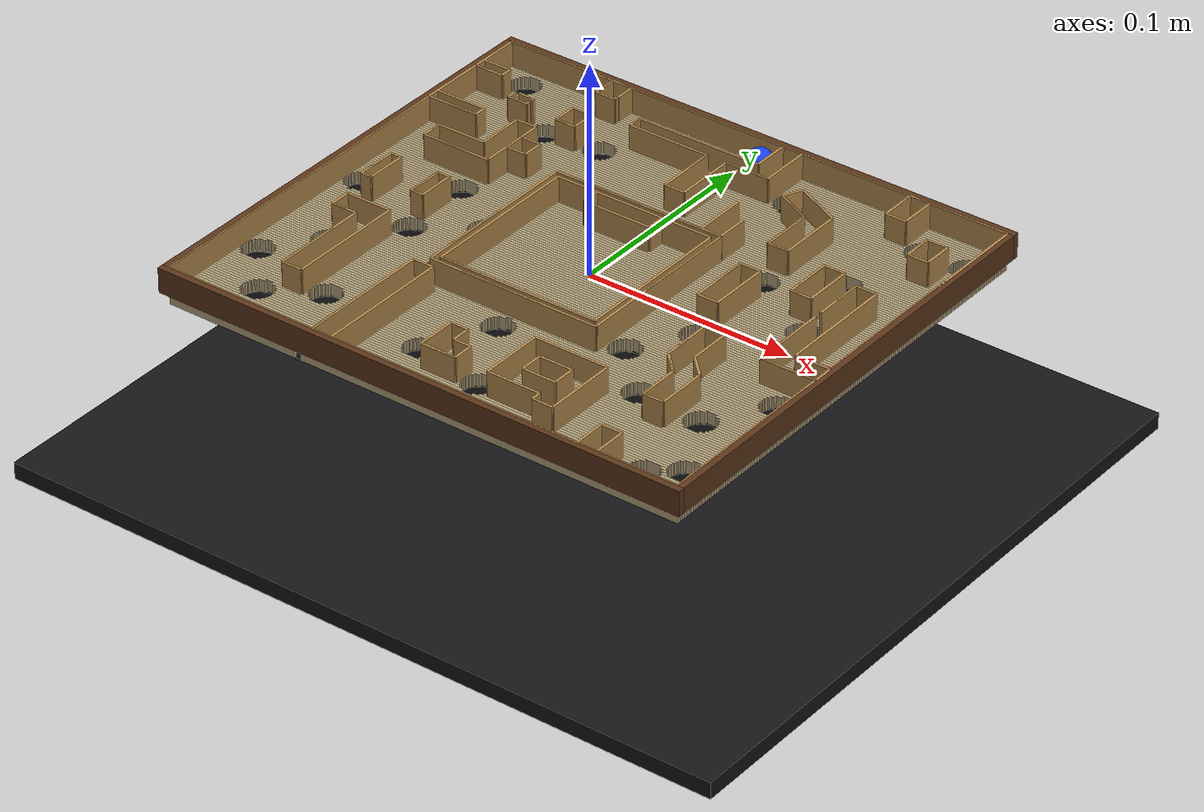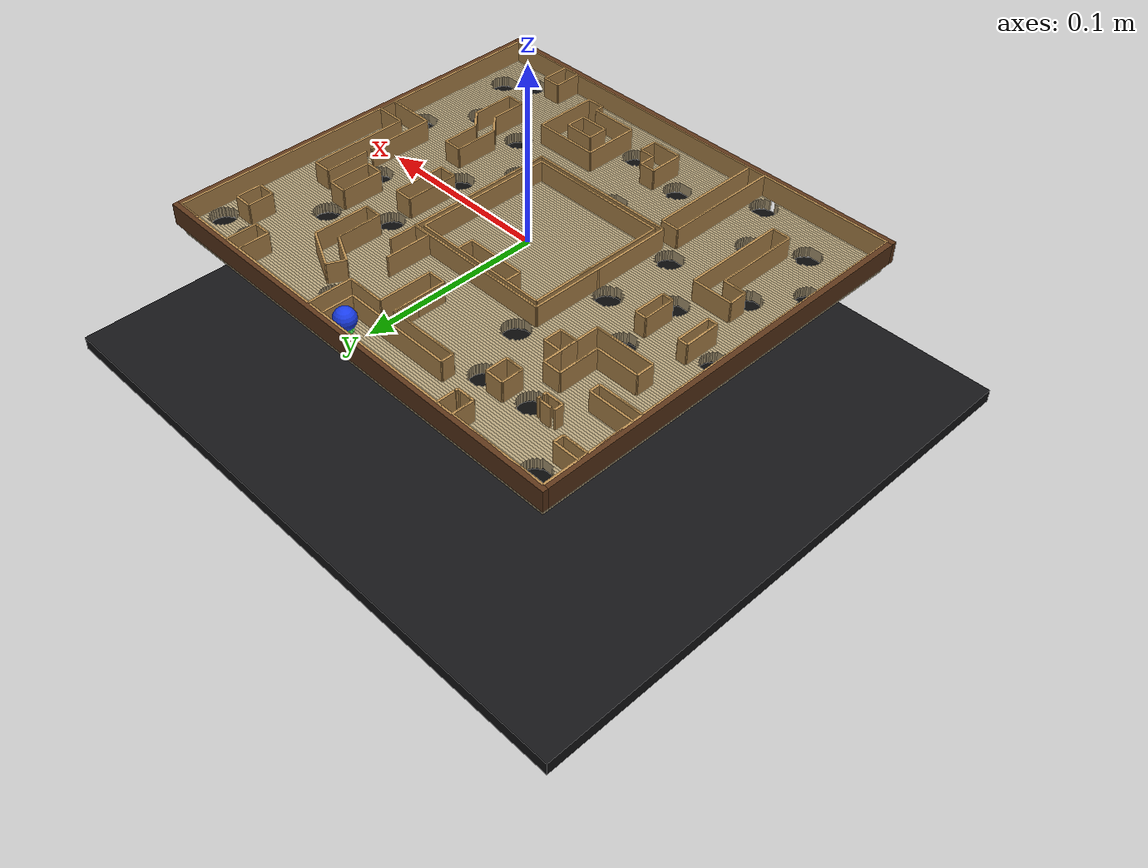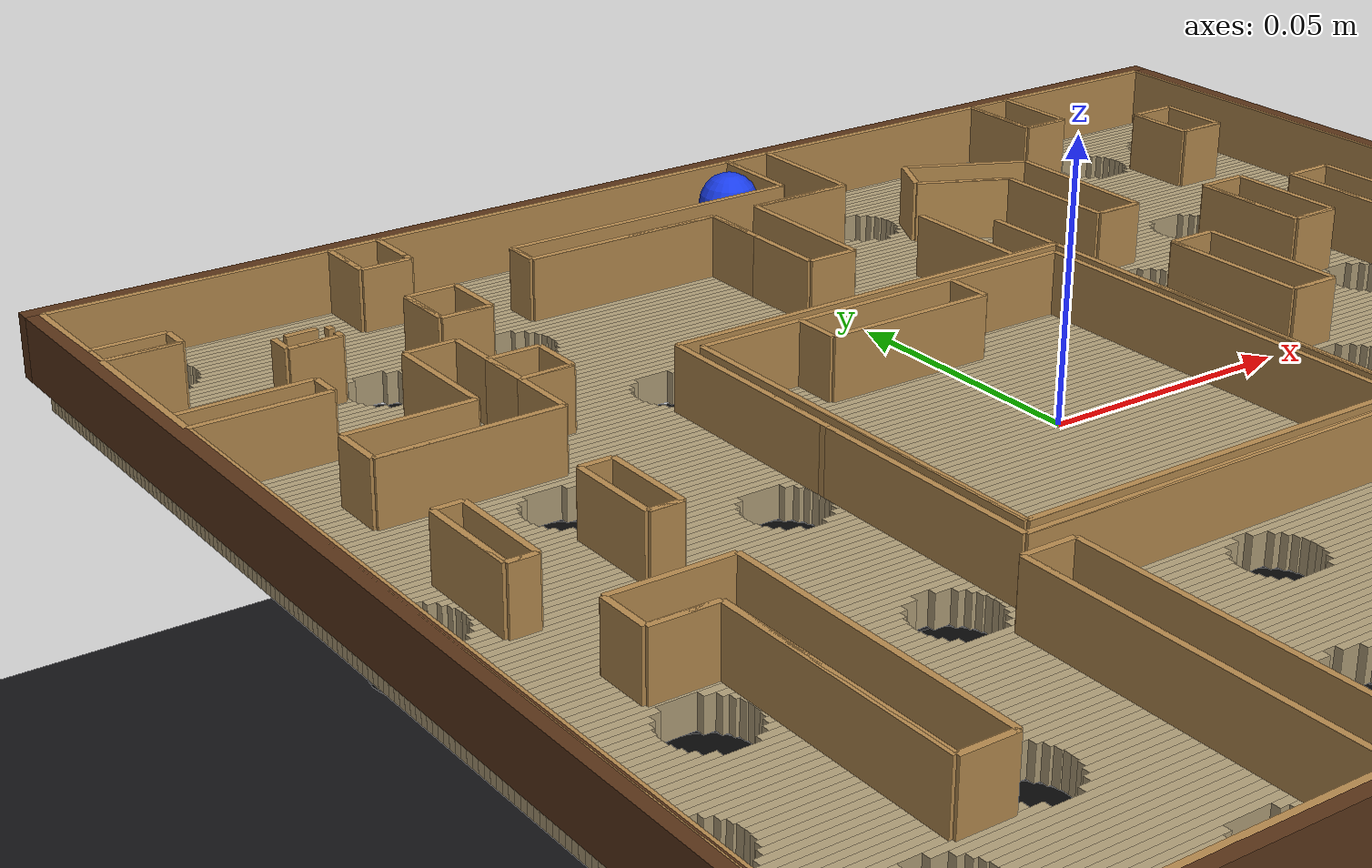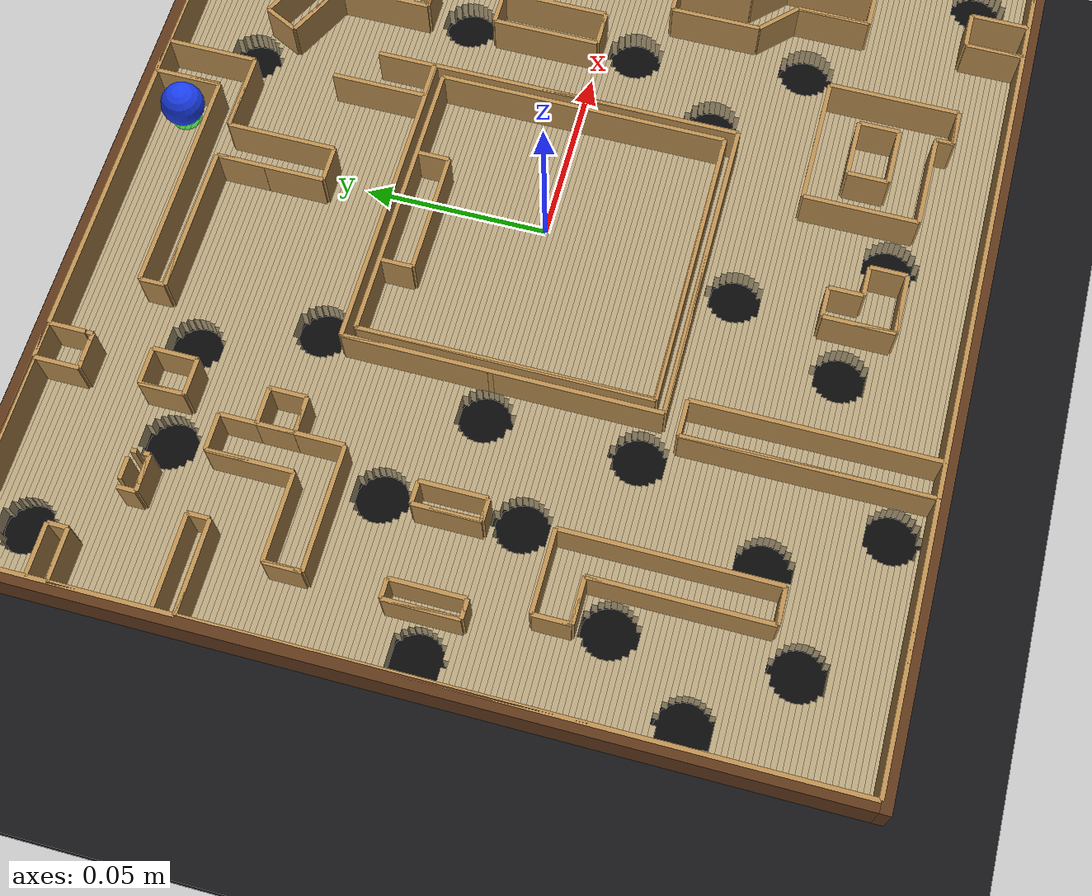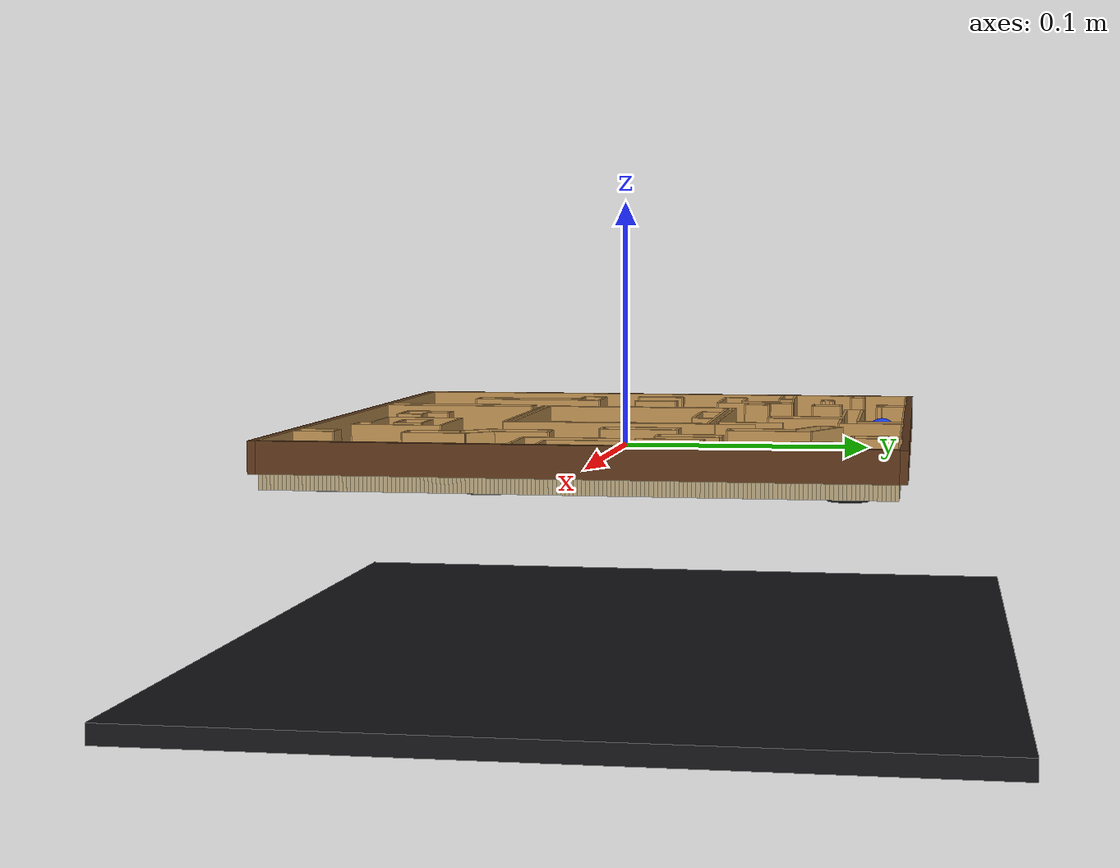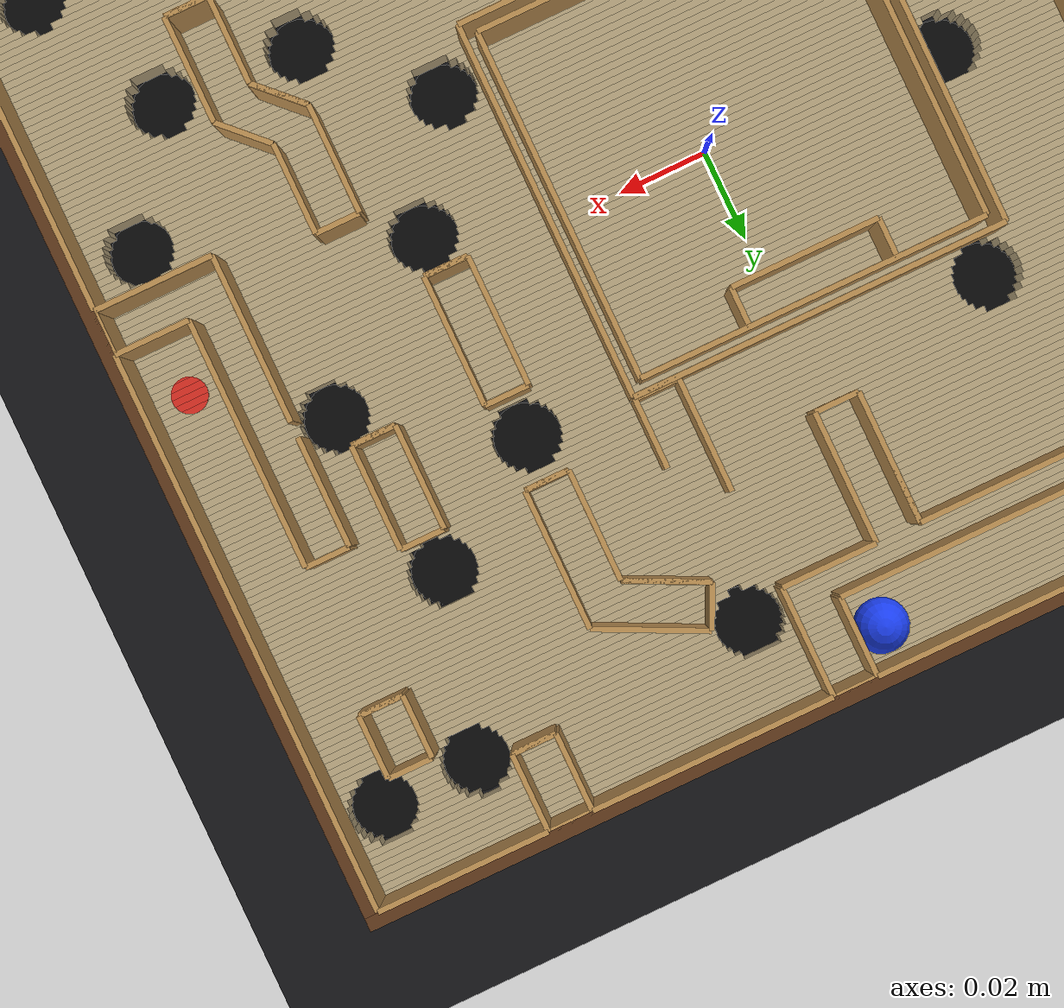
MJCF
<mujoco model="cyberrunner_custom_maze">
  <compiler angle="radian" inertiafromgeom="auto"/>
  <option timestep="0.001" gravity="0 0 -9.81" integrator="implicitfast" solver="Newton" iterations="12" tolerance="1e-9"/>
  <size nconmax="4000" njmax="12000"/>
  <visual>
    <global offwidth="900" offheight="800"/>
    <quality shadowsize="2048"/>
    <map znear="0.01" zfar="3"/>
  </visual>
  <default>
    <default class="floor">
      <geom friction="0.3 0.015 0.002" solref="0.004 1" solimp="0.95 0.99 0.001" density="650"/>
    </default>
    <default class="wall">
      <geom friction="0.35 0.02 0.003" solref="0.003 1" solimp="0.95 0.99 0.001" density="700"/>
    </default>
  </default>
  <worldbody>
    <light name="key" pos="0 -0.15 0.55" dir="0 0 -1" diffuse="0.9 0.9 0.9"/>
    <light name="fill" pos="-0.25 0.2 0.35" dir="0.4 -0.3 -1" diffuse="0.45 0.45 0.45"/>
    <camera name="top" pos="0 0 0.43" quat="1 0 0 0" mode="fixed" fovy="37"/>
    <geom name="catch_tray" type="box" pos="0 0 -0.085" size="0.18 0.16 0.004" rgba="0.08 0.08 0.09 1" friction="0.5 0.02 0.003"/>
    <body name="tilt_x_frame" pos="0 0 0">
      <inertial pos="0 0 0" mass="0.02" diaginertia="0.0001 0.0001 0.0001"/>
      <joint name="tilt_x" type="hinge" axis="1 0 0" range="-0.174532925 0.174532925" damping="0.8" armature="0.01"/>
      <body name="board" pos="0 0 0">
        <joint name="tilt_y" type="hinge" axis="0 1 0" range="-0.174532925 0.174532925" damping="0.8" armature="0.01"/>
        <geom name="floor_0" type="box" pos="-0.0964366186 -0.113751634 -0.003" size="0.0330633814 0.000748366013 0.003" rgba="0.70 0.63 0.48 1" class="floor"/><geom name="floor_1" type="box" pos="0.0347553906 -0.113751634 -0.003" size="0.0947446094 0.000748366013 0.003" rgba="0.70 0.63 0.48 1" class="floor"/><geom name="floor_2" type="box" pos="-0.0979620522 -0.112254902 -0.003" size="0.0315379478 0.000748366013 0.003" rgba="0.70 0.63 0.48 1" class="floor"/><geom name="floor_3" type="box" pos="0.0362808242 -0.112254902 -0.003" size="0.0932191758 0.000748366013 0.003" rgba="0.70 0.63 0.48 1" class="floor"/><geom name="floor_4" type="box" pos="-0.0986584489 -0.11075817 -0.003" size="0.0308415511 0.000748366013 0.003" rgba="0.70 0.63 0.48 1" class="floor"/><geom name="floor_5" type="box" pos="0.0369772209 -0.11075817 -0.003" size="0.0925227791 0.000748366013 0.003" rgba="0.70 0.63 0.48 1" class="floor"/><geom name="floor_6" type="box" pos="-0.0990661571 -0.109261438 -0.003" size="0.0304338429 0.000748366013 0.003" rgba="0.70 0.63 0.48 1" class="floor"/><geom name="floor_7" type="box" pos="0.0373849291 -0.109261438 -0.003" size="0.0921150709 0.000748366013 0.003" rgba="0.70 0.63 0.48 1" class="floor"/><geom name="floor_8" type="box" pos="-0.0992821022 -0.107764706 -0.003" size="0.0302178978 0.000748366013 0.003" rgba="0.70 0.63 0.48 1" class="floor"/><geom name="floor_9" type="box" pos="0.0229241235 -0.107764706 -0.003" size="0.0772223752 0.000748366013 0.003" rgba="0.70 0.63 0.48 1" class="floor"/><geom name="floor_10" type="box" pos="0.117288856 -0.107764706 -0.003" size="0.0122111444 0.000748366013 0.003" rgba="0.70 0.63 0.48 1" class="floor"/><geom name="floor_11" type="box" pos="-0.0993395694 -0.106267974 -0.003" size="0.0301604306 0.000748366013 0.003" rgba="0.70 0.63 0.48 1" class="floor"/><geom name="floor_12" type="box" pos="0.0217122891 -0.106267974 -0.003" size="0.0758956063 0.000748366013 0.003" rgba="0.70 0.63 0.48 1" class="floor"/><geom name="floor_13" type="box" pos="0.118558157 -0.106267974 -0.003" size="0.0109418427 0.000748366013 0.003" rgba="0.70 0.63 0.48 1" class="floor"/><geom name="floor_14" type="box" pos="-0.0992460408 -0.104771242 -0.003" size="0.0302539592 0.000748366013 0.003" rgba="0.70 0.63 0.48 1" class="floor"/><geom name="floor_15" type="box" pos="0.0209774356 -0.104771242 -0.003" size="0.07534781 0.000748366013 0.003" rgba="0.70 0.63 0.48 1" class="floor"/><geom name="floor_16" type="box" pos="0.119199482 -0.104771242 -0.003" size="0.0103005178 0.000748366013 0.003" rgba="0.70 0.63 0.48 1" class="floor"/><geom name="floor_17" type="box" pos="-0.0989890725 -0.10327451 -0.003" size="0.0305109275 0.000748366013 0.003" rgba="0.70 0.63 0.48 1" class="floor"/><geom name="floor_18" type="box" pos="0.0203451375 -0.10327451 -0.003" size="0.0752294485 0.000748366013 0.003" rgba="0.70 0.63 0.48 1" class="floor"/><geom name="floor_19" type="box" pos="0.119574812 -0.10327451 -0.003" size="0.009925188 0.000748366013 0.003" rgba="0.70 0.63 0.48 1" class="floor"/><geom name="floor_20" type="box" pos="-0.0985260513 -0.101777778 -0.003" size="0.0309739487 0.000748366013 0.003" rgba="0.70 0.63 0.48 1" class="floor"/><geom name="floor_21" type="box" pos="0.0196911476 -0.101777778 -0.003" size="0.0755015011 0.000748366013 0.003" rgba="0.70 0.63 0.48 1" class="floor"/><geom name="floor_22" type="box" pos="0.119765781 -0.101777778 -0.003" size="0.00973421931 0.000748366013 0.003" rgba="0.70 0.63 0.48 1" class="floor"/><geom name="floor_23" type="box" pos="-0.0977269567 -0.100281046 -0.003" size="0.0317730433 0.000748366013 0.003" rgba="0.70 0.63 0.48 1" class="floor"/><geom name="floor_24" type="box" pos="0.0188571324 -0.100281046 -0.003" size="0.076265675 0.000748366013 0.003" rgba="0.70 0.63 0.48 1" class="floor"/><geom name="floor_25" type="box" pos="0.119800701 -0.100281046 -0.003" size="0.00969929869 0.000748366013 0.003" rgba="0.70 0.63 0.48 1" class="floor"/><geom name="floor_26" type="box" pos="-0.059213715 -0.0987843137 -0.003" size="0.070286285 0.000748366013 0.003" rgba="0.70 0.63 0.48 1" class="floor"/><geom name="floor_27" type="box" pos="0.0556456133 -0.0987843137 -0.003" size="0.0397104314 0.000748366013 0.003" rgba="0.70 0.63 0.48 1" class="floor"/><geom name="floor_28" type="box" pos="0.119684083 -0.0987843137 -0.003" size="0.00981591735 0.000748366013 0.003" rgba="0.70 0.63 0.48 1" class="floor"/><geom name="floor_29" type="box" pos="-0.117746347 -0.0972875817 -0.003" size="0.0117536532 0.000748366013 0.003" rgba="0.70 0.63 0.48 1" class="floor"/><geom name="floor_30" type="box" pos="-0.0445750827 -0.0972875817 -0.003" size="0.0530880057 0.000748366013 0.003" rgba="0.70 0.63 0.48 1" class="floor"/><geom name="floor_31" type="box" pos="0.0572094114 -0.0972875817 -0.003" size="0.0387145825 0.000748366013 0.003" rgba="0.70 0.63 0.48 1" class="floor"/><geom name="floor_32" type="box" pos="0.110558918 -0.0972875817 -0.003" size="0.00125870222 0.000748366013 0.003" rgba="0.70 0.63 0.48 1" class="floor"/><geom name="floor_33" type="box" pos="0.124889515 -0.0972875817 -0.003" size="0.00461048526 0.000748366013 0.003" rgba="0.70 0.63 0.48 1" class="floor"/><geom name="floor_34" type="box" pos="-0.118569829 -0.0957908497 -0.003" size="0.0109301713 0.000748366013 0.003" rgba="0.70 0.63 0.48 1" class="floor"/><geom name="floor_35" type="box" pos="-0.0443956927 -0.0957908497 -0.003" size="0.0516204318 0.000748366013 0.003" rgba="0.70 0.63 0.48 1" class="floor"/><geom name="floor_36" type="box" pos="0.0583545485 -0.0957908497 -0.003" size="0.0385715355 0.000748366013 0.003" rgba="0.70 0.63 0.48 1" class="floor"/><geom name="floor_37" type="box" pos="0.10924933 -0.0957908497 -0.003" size="0.000951203684 0.000748366013 0.003" rgba="0.70 0.63 0.48 1" class="floor"/><geom name="floor_38" type="box" pos="0.125698058 -0.0957908497 -0.003" size="0.0038019417 0.000748366013 0.003" rgba="0.70 0.63 0.48 1" class="floor"/><geom name="floor_39" type="box" pos="-0.119045042 -0.0942941176 -0.003" size="0.0104549576 0.000748366013 0.003" rgba="0.70 0.63 0.48 1" class="floor"/><geom name="floor_40" type="box" pos="-0.044297482 -0.0942941176 -0.003" size="0.0507682153 0.000748366013 0.003" rgba="0.70 0.63 0.48 1" class="floor"/><geom name="floor_41" type="box" pos="0.0596092103 -0.0942941176 -0.003" size="0.0390721916 0.000748366013 0.003" rgba="0.70 0.63 0.48 1" class="floor"/><geom name="floor_42" type="box" pos="0.107903883 -0.0942941176 -0.003" size="0.00136107526 0.000748366013 0.003" rgba="0.70 0.63 0.48 1" class="floor"/><geom name="floor_43" type="box" pos="0.126165846 -0.0942941176 -0.003" size="0.00333415431 0.000748366013 0.003" rgba="0.70 0.63 0.48 1" class="floor"/><geom name="floor_44" type="box" pos="-0.119310776 -0.0927973856 -0.003" size="0.0101892242 0.000748366013 0.003" rgba="0.70 0.63 0.48 1" class="floor"/><geom name="floor_45" type="box" pos="-0.0442240254 -0.0927973856 -0.003" size="0.050310205 0.000748366013 0.003" rgba="0.70 0.63 0.48 1" class="floor"/><geom name="floor_46" type="box" pos="0.0648328589 -0.0927973856 -0.003" size="0.0439112865 0.000748366013 0.003" rgba="0.70 0.63 0.48 1" class="floor"/><geom name="floor_47" type="box" pos="0.126426252 -0.0927973856 -0.003" size="0.00307374773 0.000748366013 0.003" rgba="0.70 0.63 0.48 1" class="floor"/><geom name="floor_48" type="box" pos="-0.119411855 -0.0913006536 -0.003" size="0.0100881453 0.000748366013 0.003" rgba="0.70 0.63 0.48 1" class="floor"/><geom name="floor_49" type="box" pos="-0.0601653299 -0.0913006536 -0.003" size="0.0341667427 0.000748366013 0.003" rgba="0.70 0.63 0.48 1" class="floor"/><geom name="floor_50" type="box" pos="-0.00560471931 -0.0913006536 -0.003" size="0.0116186735 0.000748366013 0.003" rgba="0.70 0.63 0.48 1" class="floor"/><geom name="floor_51" type="box" pos="0.0647724748 -0.0913006536 -0.003" size="0.0437786771 0.000748366013 0.003" rgba="0.70 0.63 0.48 1" class="floor"/><geom name="floor_52" type="box" pos="0.126522749 -0.0913006536 -0.003" size="0.00297725095 0.000748366013 0.003" rgba="0.70 0.63 0.48 1" class="floor"/><geom name="floor_53" type="box" pos="-0.119361806 -0.0898039216 -0.003" size="0.010138194 0.000748366013 0.003" rgba="0.70 0.63 0.48 1" class="floor"/><geom name="floor_54" type="box" pos="-0.0609888635 -0.0898039216 -0.003" size="0.0334433066 0.000748366013 0.003" rgba="0.70 0.63 0.48 1" class="floor"/><geom name="floor_55" type="box" pos="-0.00471584732 -0.0898039216 -0.003" size="0.0109605757 0.000748366013 0.003" rgba="0.70 0.63 0.48 1" class="floor"/><geom name="floor_56" type="box" pos="0.0647116333 -0.0898039216 -0.003" size="0.0439486097 0.000748366013 0.003" rgba="0.70 0.63 0.48 1" class="floor"/><geom name="floor_57" type="box" pos="0.126468204 -0.0898039216 -0.003" size="0.00303179646 0.000748366013 0.003" rgba="0.70 0.63 0.48 1" class="floor"/><geom name="floor_58" type="box" pos="-0.119154134 -0.0883071895 -0.003" size="0.0103458658 0.000748366013 0.003" rgba="0.70 0.63 0.48 1" class="floor"/><geom name="floor_59" type="box" pos="-0.0616463685 -0.0883071895 -0.003" size="0.0332011451 0.000748366013 0.003" rgba="0.70 0.63 0.48 1" class="floor"/><geom name="floor_60" type="box" pos="-0.00398349514 -0.0883071895 -0.003" size="0.0107932614 0.000748366013 0.003" rgba="0.70 0.63 0.48 1" class="floor"/><geom name="floor_61" type="box" pos="0.0646417945 -0.0883071895 -0.003" size="0.0444438087 0.000748366013 0.003" rgba="0.70 0.63 0.48 1" class="floor"/><geom name="floor_62" type="box" pos="0.126255523 -0.0883071895 -0.003" size="0.00324447658 0.000748366013 0.003" rgba="0.70 0.63 0.48 1" class="floor"/><geom name="floor_63" type="box" pos="-0.118757254 -0.0868104575 -0.003" size="0.0107427458 0.000748366013 0.003" rgba="0.70 0.63 0.48 1" class="floor"/><geom name="floor_64" type="box" pos="-0.0622906234 -0.0868104575 -0.003" size="0.0333506501 0.000748366013 0.003" rgba="0.70 0.63 0.48 1" class="floor"/><geom name="floor_65" type="box" pos="-0.00323716006 -0.0868104575 -0.003" size="0.0110448466 0.000748366013 0.003" rgba="0.70 0.63 0.48 1" class="floor"/><geom name="floor_66" type="box" pos="0.0645462567 -0.0868104575 -0.003" size="0.0453461913 0.000748366013 0.003" rgba="0.70 0.63 0.48 1" class="floor"/><geom name="floor_67" type="box" pos="0.125852101 -0.0868104575 -0.003" size="0.00364789904 0.000748366013 0.003" rgba="0.70 0.63 0.48 1" class="floor"/><geom name="floor_68" type="box" pos="-0.118079644 -0.0853137255 -0.003" size="0.0114203564 0.000748366013 0.003" rgba="0.70 0.63 0.48 1" class="floor"/><geom name="floor_69" type="box" pos="-0.0630534367 -0.0853137255 -0.003" size="0.033943058 0.000748366013 0.003" rgba="0.70 0.63 0.48 1" class="floor"/><geom name="floor_70" type="box" pos="-0.00227880749 -0.0853137255 -0.003" size="0.0118327938 0.000748366013 0.003" rgba="0.70 0.63 0.48 1" class="floor"/><geom name="floor_71" type="box" pos="0.0643620219 -0.0853137255 -0.003" size="0.0469082562 0.000748366013 0.003" rgba="0.70 0.63 0.48 1" class="floor"/><geom name="floor_72" type="box" pos="0.125163186 -0.0853137255 -0.003" size="0.00433681403 0.000748366013 0.003" rgba="0.70 0.63 0.48 1" class="floor"/><geom name="floor_73" type="box" pos="-0.116655173 -0.0838169935 -0.003" size="0.0128448267 0.000748366013 0.003" rgba="0.70 0.63 0.48 1" class="floor"/><geom name="floor_74" type="box" pos="-0.0900219924 -0.0838169935 -0.003" size="0.00982344299 0.000748366013 0.003" rgba="0.70 0.63 0.48 1" class="floor"/><geom name="floor_75" type="box" pos="-0.0516977095 -0.0838169935 -0.003" size="0.0227187311 0.000748366013 0.003" rgba="0.70 0.63 0.48 1" class="floor"/><geom name="floor_76" type="box" pos="0.0499965394 -0.0838169935 -0.003" size="0.064239541 0.000748366013 0.003" rgba="0.70 0.63 0.48 1" class="floor"/><geom name="floor_77" type="box" pos="0.123680285 -0.0838169935 -0.003" size="0.00581971517 0.000748366013 0.003" rgba="0.70 0.63 0.48 1" class="floor"/><geom name="floor_78" type="box" pos="-0.105993821 -0.0823202614 -0.003" size="0.0235061787 0.000748366013 0.003" rgba="0.70 0.63 0.48 1" class="floor"/><geom name="floor_79" type="box" pos="-0.0503279713 -0.0823202614 -0.003" size="0.0217993761 0.000748366013 0.003" rgba="0.70 0.63 0.48 1" class="floor"/><geom name="floor_80" type="box" pos="0.0574033076 -0.0823202614 -0.003" size="0.0720966924 0.000748366013 0.003" rgba="0.70 0.63 0.48 1" class="floor"/><geom name="floor_81" type="box" pos="-0.106598636 -0.0808235294 -0.003" size="0.022901364 0.000748366013 0.003" rgba="0.70 0.63 0.48 1" class="floor"/><geom name="floor_82" type="box" pos="-0.0493032213 -0.0808235294 -0.003" size="0.0216144968 0.000748366013 0.003" rgba="0.70 0.63 0.48 1" class="floor"/><geom name="floor_83" type="box" pos="0.0569833723 -0.0808235294 -0.003" size="0.0725166277 0.000748366013 0.003" rgba="0.70 0.63 0.48 1" class="floor"/><geom name="floor_84" type="box" pos="-0.106951428 -0.0793267974 -0.003" size="0.0225485717 0.000748366013 0.003" rgba="0.70 0.63 0.48 1" class="floor"/><geom name="floor_85" type="box" pos="-0.0482323395 -0.0793267974 -0.003" size="0.021979794 0.000748366013 0.003" rgba="0.70 0.63 0.48 1" class="floor"/><geom name="floor_86" type="box" pos="0.0562652828 -0.0793267974 -0.003" size="0.0732347172 0.000748366013 0.003" rgba="0.70 0.63 0.48 1" class="floor"/><geom name="floor_87" type="box" pos="-0.107124589 -0.0778300654 -0.003" size="0.0223754109 0.000748366013 0.003" rgba="0.70 0.63 0.48 1" class="floor"/><geom name="floor_88" type="box" pos="-0.0463843123 -0.0778300654 -0.003" size="0.0234814996 0.000748366013 0.003" rgba="0.70 0.63 0.48 1" class="floor"/><geom name="floor_89" type="box" pos="0.0545904164 -0.0778300654 -0.003" size="0.0749095836 0.000748366013 0.003" rgba="0.70 0.63 0.48 1" class="floor"/><geom name="floor_90" type="box" pos="-0.107143157 -0.0763333333 -0.003" size="0.0223568432 0.000748366013 0.003" rgba="0.70 0.63 0.48 1" class="floor"/><geom name="floor_91" type="box" pos="0.0298356618 -0.0763333333 -0.003" size="0.0996643382 0.000748366013 0.003" rgba="0.70 0.63 0.48 1" class="floor"/><geom name="floor_92" type="box" pos="-0.10700952 -0.0748366013 -0.003" size="0.0224904796 0.000748366013 0.003" rgba="0.70 0.63 0.48 1" class="floor"/><geom name="floor_93" type="box" pos="0.0297020254 -0.0748366013 -0.003" size="0.0997979746 0.000748366013 0.003" rgba="0.70 0.63 0.48 1" class="floor"/><geom name="floor_94" type="box" pos="-0.127726606 -0.0733398693 -0.003" size="0.0017733942 0.000748366013 0.003" rgba="0.70 0.63 0.48 1" class="floor"/><geom name="floor_95" type="box" pos="-0.100602545 -0.0733398693 -0.003" size="0.0166920473 0.000748366013 0.003" rgba="0.70 0.63 0.48 1" class="floor"/><geom name="floor_96" type="box" pos="0.0293977539 -0.0733398693 -0.003" size="0.100102246 0.000748366013 0.003" rgba="0.70 0.63 0.48 1" class="floor"/><geom name="floor_97" type="box" pos="-0.128513035 -0.0718431373 -0.003" size="0.000986964727 0.000748366013 0.003" rgba="0.70 0.63 0.48 1" class="floor"/><geom name="floor_98" type="box" pos="-0.0992855565 -0.0718431373 -0.003" size="0.016436177 0.000748366013 0.003" rgba="0.70 0.63 0.48 1" class="floor"/><geom name="floor_99" type="box" pos="0.0288671948 -0.0718431373 -0.003" size="0.100632805 0.000748366013 0.003" rgba="0.70 0.63 0.48 1" class="floor"/><geom name="floor_100" type="box" pos="-0.128969584 -0.0703464052 -0.003" size="0.000530415951 0.000748366013 0.003" rgba="0.70 0.63 0.48 1" class="floor"/><geom name="floor_101" type="box" pos="-0.0978845997 -0.0703464052 -0.003" size="0.0169240362 0.000748366013 0.003" rgba="0.70 0.63 0.48 1" class="floor"/><geom name="floor_102" type="box" pos="0.0279227867 -0.0703464052 -0.003" size="0.101577213 0.000748366013 0.003" rgba="0.70 0.63 0.48 1" class="floor"/><geom name="floor_103" type="box" pos="-0.129221859 -0.0688496732 -0.003" size="0.00027814132 0.000748366013 0.003" rgba="0.70 0.63 0.48 1" class="floor"/><geom name="floor_104" type="box" pos="0.00759795668 -0.0688496732 -0.003" size="0.121902043 0.000748366013 0.003" rgba="0.70 0.63 0.48 1" class="floor"/><geom name="floor_105" type="box" pos="-0.129311322 -0.0673529412 -0.003" size="0.000188678108 0.000748366013 0.003" rgba="0.70 0.63 0.48 1" class="floor"/><geom name="floor_106" type="box" pos="0.00768741989 -0.0673529412 -0.003" size="0.12181258 0.000748366013 0.003" rgba="0.70 0.63 0.48 1" class="floor"/><geom name="floor_107" type="box" pos="-0.129249842 -0.0658562092 -0.003" size="0.00025015847 0.000748366013 0.003" rgba="0.70 0.63 0.48 1" class="floor"/><geom name="floor_108" type="box" pos="-0.00893153432 -0.0658562092 -0.003" size="0.105316587 0.000748366013 0.003" rgba="0.70 0.63 0.48 1" class="floor"/><geom name="floor_109" type="box" pos="0.116788986 -0.0658562092 -0.003" size="0.0127110141 0.000748366013 0.003" rgba="0.70 0.63 0.48 1" class="floor"/><geom name="floor_110" type="box" pos="-0.129029398 -0.0643594771 -0.003" size="0.00047060215 0.000748366013 0.003" rgba="0.70 0.63 0.48 1" class="floor"/><geom name="floor_111" type="box" pos="-0.0247023251 -0.0643594771 -0.003" size="0.0899866832 0.000748366013 0.003" rgba="0.70 0.63 0.48 1" class="floor"/><geom name="floor_112" type="box" pos="0.0831043052 -0.0643594771 -0.003" size="0.0114855252 0.000748366013 0.003" rgba="0.70 0.63 0.48 1" class="floor"/><geom name="floor_113" type="box" pos="0.117686597 -0.0643594771 -0.003" size="0.0118134032 0.000748366013 0.003" rgba="0.70 0.63 0.48 1" class="floor"/><geom name="floor_114" type="box" pos="-0.128615758 -0.0628627451 -0.003" size="0.000884242298 0.000748366013 0.003" rgba="0.70 0.63 0.48 1" class="floor"/><geom name="floor_115" type="box" pos="-0.0261848069 -0.0628627451 -0.003" size="0.0893314817 0.000748366013 0.003" rgba="0.70 0.63 0.48 1" class="floor"/><geom name="floor_116" type="box" pos="0.0836630163 -0.0628627451 -0.003" size="0.00990655317 0.000748366013 0.003" rgba="0.70 0.63 0.48 1" class="floor"/><geom name="floor_117" type="box" pos="0.118196727 -0.0628627451 -0.003" size="0.0113032727 0.000748366013 0.003" rgba="0.70 0.63 0.48 1" class="floor"/><geom name="floor_118" type="box" pos="-0.127908902 -0.0613660131 -0.003" size="0.00159109785 0.000748366013 0.003" rgba="0.70 0.63 0.48 1" class="floor"/><geom name="floor_119" type="box" pos="-0.0274707848 -0.0613660131 -0.003" size="0.0894592149 0.000748366013 0.003" rgba="0.70 0.63 0.48 1" class="floor"/><geom name="floor_120" type="box" pos="0.0839518543 -0.0613660131 -0.003" size="0.00903714635 0.000748366013 0.003" rgba="0.70 0.63 0.48 1" class="floor"/><geom name="floor_121" type="box" pos="0.118487012 -0.0613660131 -0.003" size="0.0110129883 0.000748366013 0.003" rgba="0.70 0.63 0.48 1" class="floor"/><geom name="floor_122" type="box" pos="-0.126317279 -0.059869281 -0.003" size="0.00318272081 0.000748366013 0.003" rgba="0.70 0.63 0.48 1" class="floor"/><geom name="floor_123" type="box" pos="-0.0652246925 -0.059869281 -0.003" size="0.0548885531 0.000748366013 0.003" rgba="0.70 0.63 0.48 1" class="floor"/><geom name="floor_124" type="box" pos="0.0298090101 -0.059869281 -0.003" size="0.0315065927 0.000748366013 0.003" rgba="0.70 0.63 0.48 1" class="floor"/><geom name="floor_125" type="box" pos="0.0841663281 -0.059869281 -0.003" size="0.00857879289 0.000748366013 0.003" rgba="0.70 0.63 0.48 1" class="floor"/><geom name="floor_126" type="box" pos="0.118608951 -0.059869281 -0.003" size="0.0108910485 0.000748366013 0.003" rgba="0.70 0.63 0.48 1" class="floor"/><geom name="floor_127" type="box" pos="-0.0707067363 -0.058372549 -0.003" size="0.0587932637 0.000748366013 0.003" rgba="0.70 0.63 0.48 1" class="floor"/><geom name="floor_128" type="box" pos="0.0304376761 -0.058372549 -0.003" size="0.0305579255 0.000748366013 0.003" rgba="0.70 0.63 0.48 1" class="floor"/><geom name="floor_129" type="box" pos="0.0843561122 -0.058372549 -0.003" size="0.00844857576 0.000748366013 0.003" rgba="0.70 0.63 0.48 1" class="floor"/><geom name="floor_130" type="box" pos="0.118579168 -0.058372549 -0.003" size="0.010920832 0.000748366013 0.003" rgba="0.70 0.63 0.48 1" class="floor"/><geom name="floor_131" type="box" pos="-0.0711644354 -0.056875817 -0.003" size="0.0583355646 0.000748366013 0.003" rgba="0.70 0.63 0.48 1" class="floor"/><geom name="floor_132" type="box" pos="0.0308890426 -0.056875817 -0.003" size="0.0300938938 0.000748366013 0.003" rgba="0.70 0.63 0.48 1" class="floor"/><geom name="floor_133" type="box" pos="0.0845477919 -0.056875817 -0.003" size="0.00862759031 0.000748366013 0.003" rgba="0.70 0.63 0.48 1" class="floor"/><geom name="floor_134" type="box" pos="0.118393821 -0.056875817 -0.003" size="0.0111061791 0.000748366013 0.003" rgba="0.70 0.63 0.48 1" class="floor"/><geom name="floor_135" type="box" pos="-0.0714175462 -0.055379085 -0.003" size="0.0580824538 0.000748366013 0.003" rgba="0.70 0.63 0.48 1" class="floor"/><geom name="floor_136" type="box" pos="0.0312886751 -0.055379085 -0.003" size="0.0299873046 0.000748366013 0.003" rgba="0.70 0.63 0.48 1" class="floor"/><geom name="floor_137" type="box" pos="0.0847694377 -0.055379085 -0.003" size="0.00914227946 0.000748366013 0.003" rgba="0.70 0.63 0.48 1" class="floor"/><geom name="floor_138" type="box" pos="0.118025653 -0.055379085 -0.003" size="0.0114743466 0.000748366013 0.003" rgba="0.70 0.63 0.48 1" class="floor"/><geom name="floor_139" type="box" pos="-0.0715077349 -0.0538823529 -0.003" size="0.0579922651 0.000748366013 0.003" rgba="0.70 0.63 0.48 1" class="floor"/><geom name="floor_140" type="box" pos="0.0316987356 -0.0538823529 -0.003" size="0.0302169879 0.000748366013 0.003" rgba="0.70 0.63 0.48 1" class="floor"/><geom name="floor_141" type="box" pos="0.0850791356 -0.0538823529 -0.003" size="0.0100917211 0.000748366013 0.003" rgba="0.70 0.63 0.48 1" class="floor"/><geom name="floor_142" type="box" pos="0.117396084 -0.0538823529 -0.003" size="0.0121039164 0.000748366013 0.003" rgba="0.70 0.63 0.48 1" class="floor"/><geom name="floor_143" type="box" pos="-0.0714469716 -0.0523856209 -0.003" size="0.0580530284 0.000748366013 0.003" rgba="0.70 0.63 0.48 1" class="floor"/><geom name="floor_144" type="box" pos="0.0321918088 -0.0523856209 -0.003" size="0.0308315876 0.000748366013 0.003" rgba="0.70 0.63 0.48 1" class="floor"/><geom name="floor_145" type="box" pos="0.085751763 -0.0523856209 -0.003" size="0.0118720214 0.000748366013 0.003" rgba="0.70 0.63 0.48 1" class="floor"/><geom name="floor_146" type="box" pos="0.11616962 -0.0523856209 -0.003" size="0.0133303802 0.000748366013 0.003" rgba="0.70 0.63 0.48 1" class="floor"/><geom name="floor_147" type="box" pos="-0.11791595 -0.0508888889 -0.003" size="0.0115840502 0.000748366013 0.003" rgba="0.70 0.63 0.48 1" class="floor"/><geom name="floor_148" type="box" pos="-0.0565309281 -0.0508888889 -0.003" size="0.0435762623 0.000748366013 0.003" rgba="0.70 0.63 0.48 1" class="floor"/><geom name="floor_149" type="box" pos="0.0329736249 -0.0508888889 -0.003" size="0.0320526811 0.000748366013 0.003" rgba="0.70 0.63 0.48 1" class="floor"/><geom name="floor_150" type="box" pos="0.100688416 -0.0508888889 -0.003" size="0.028811584 0.000748366013 0.003" rgba="0.70 0.63 0.48 1" class="floor"/><geom name="floor_151" type="box" pos="-0.118999523 -0.0493921569 -0.003" size="0.0105004772 0.000748366013 0.003" rgba="0.70 0.63 0.48 1" class="floor"/><geom name="floor_152" type="box" pos="-0.0550347788 -0.0493921569 -0.003" size="0.0429052657 0.000748366013 0.003" rgba="0.70 0.63 0.48 1" class="floor"/><geom name="floor_153" type="box" pos="0.0647978956 -0.0493921569 -0.003" size="0.0647021044 0.000748366013 0.003" rgba="0.70 0.63 0.48 1" class="floor"/><geom name="floor_154" type="box" pos="-0.119583865 -0.0478954248 -0.003" size="0.00991613512 0.000748366013 0.003" rgba="0.70 0.63 0.48 1" class="floor"/><geom name="floor_155" type="box" pos="-0.0537454658 -0.0478954248 -0.003" size="0.0430258945 0.000748366013 0.003" rgba="0.70 0.63 0.48 1" class="floor"/><geom name="floor_156" type="box" pos="0.0640929246 -0.0478954248 -0.003" size="0.0654070754 0.000748366013 0.003" rgba="0.70 0.63 0.48 1" class="floor"/><geom name="floor_157" type="box" pos="-0.119923641 -0.0463986928 -0.003" size="0.00957635903 0.000748366013 0.003" rgba="0.70 0.63 0.48 1" class="floor"/><geom name="floor_158" type="box" pos="-0.0788152118 -0.0463986928 -0.003" size="0.0172765963 0.000748366013 0.003" rgba="0.70 0.63 0.48 1" class="floor"/><geom name="floor_159" type="box" pos="-0.030292831 -0.0463986928 -0.003" size="0.0227312895 0.000748366013 0.003" rgba="0.70 0.63 0.48 1" class="floor"/><geom name="floor_160" type="box" pos="0.0625139097 -0.0463986928 -0.003" size="0.0669860903 0.000748366013 0.003" rgba="0.70 0.63 0.48 1" class="floor"/><geom name="floor_161" type="box" pos="-0.120086358 -0.0449019608 -0.003" size="0.00941364167 0.000748366013 0.003" rgba="0.70 0.63 0.48 1" class="floor"/><geom name="floor_162" type="box" pos="-0.0794550578 -0.0449019608 -0.003" size="0.0163113156 0.000748366013 0.003" rgba="0.70 0.63 0.48 1" class="floor"/><geom name="floor_163" type="box" pos="0.0390405031 -0.0449019608 -0.003" size="0.0904594969 0.000748366013 0.003" rgba="0.70 0.63 0.48 1" class="floor"/><geom name="floor_164" type="box" pos="-0.120095227 -0.0434052288 -0.003" size="0.00940477277 0.000748366013 0.003" rgba="0.70 0.63 0.48 1" class="floor"/><geom name="floor_165" type="box" pos="-0.079910966 -0.0434052288 -0.003" size="0.0158376695 0.000748366013 0.003" rgba="0.70 0.63 0.48 1" class="floor"/><geom name="floor_166" type="box" pos="0.0395052802 -0.0434052288 -0.003" size="0.0899947198 0.000748366013 0.003" rgba="0.70 0.63 0.48 1" class="floor"/><geom name="floor_167" type="box" pos="-0.119951388 -0.0419084967 -0.003" size="0.00954861244 0.000748366013 0.003" rgba="0.70 0.63 0.48 1" class="floor"/><geom name="floor_168" type="box" pos="-0.0803130425 -0.0419084967 -0.003" size="0.0157232724 0.000748366013 0.003" rgba="0.70 0.63 0.48 1" class="floor"/><geom name="floor_169" type="box" pos="-0.00453361333 -0.0419084967 -0.003" size="0.0454393526 0.000748366013 0.003" rgba="0.70 0.63 0.48 1" class="floor"/><geom name="floor_170" type="box" pos="0.0893110003 -0.0419084967 -0.003" size="0.0401889997 0.000748366013 0.003" rgba="0.70 0.63 0.48 1" class="floor"/><geom name="floor_171" type="box" pos="-0.11963478 -0.0404117647 -0.003" size="0.00986522032 0.000748366013 0.003" rgba="0.70 0.63 0.48 1" class="floor"/><geom name="floor_172" type="box" pos="-0.0807242749 -0.0404117647 -0.003" size="0.0159452557 0.000748366013 0.003" rgba="0.70 0.63 0.48 1" class="floor"/><geom name="floor_173" type="box" pos="-0.00527542308 -0.0404117647 -0.003" size="0.0445082937 0.000748366013 0.003" rgba="0.70 0.63 0.48 1" class="floor"/><geom name="floor_174" type="box" pos="0.0901474347 -0.0404117647 -0.003" size="0.0393525653 0.000748366013 0.003" rgba="0.70 0.63 0.48 1" class="floor"/><geom name="floor_175" type="box" pos="-0.119085858 -0.0389150327 -0.003" size="0.010414142 0.000748366013 0.003" rgba="0.70 0.63 0.48 1" class="floor"/><geom name="floor_176" type="box" pos="-0.0812168091 -0.0389150327 -0.003" size="0.016550565 0.000748366013 0.003" rgba="0.70 0.63 0.48 1" class="floor"/><geom name="floor_177" type="box" pos="-0.00581335622 -0.0389150327 -0.003" size="0.0440831357 0.000748366013 0.003" rgba="0.70 0.63 0.48 1" class="floor"/><geom name="floor_178" type="box" pos="0.0828236702 -0.0389150327 -0.003" size="0.0310657097 0.000748366013 0.003" rgba="0.70 0.63 0.48 1" class="floor"/><geom name="floor_179" type="box" pos="0.125802393 -0.0389150327 -0.003" size="0.00369760697 0.000748366013 0.003" rgba="0.70 0.63 0.48 1" class="floor"/><geom name="floor_180" type="box" pos="-0.118096813 -0.0374183007 -0.003" size="0.0114031873 0.000748366013 0.003" rgba="0.70 0.63 0.48 1" class="floor"/><geom name="floor_181" type="box" pos="-0.0819911168 -0.0374183007 -0.003" size="0.0177543479 0.000748366013 0.003" rgba="0.70 0.63 0.48 1" class="floor"/><geom name="floor_182" type="box" pos="-0.00629833994 -0.0374183007 -0.003" size="0.0440276271 0.000748366013 0.003" rgba="0.70 0.63 0.48 1" class="floor"/><geom name="floor_183" type="box" pos="0.0822573839 -0.0374183007 -0.003" size="0.0299589311 0.000748366013 0.003" rgba="0.70 0.63 0.48 1" class="floor"/><geom name="floor_184" type="box" pos="0.126638926 -0.0374183007 -0.003" size="0.00286107448 0.000748366013 0.003" rgba="0.70 0.63 0.48 1" class="floor"/><geom name="floor_185" type="box" pos="-0.0964622632 -0.0359215686 -0.003" size="0.0330377368 0.000748366013 0.003" rgba="0.70 0.63 0.48 1" class="floor"/><geom name="floor_186" type="box" pos="-0.00680940618 -0.0359215686 -0.003" size="0.0443288034 0.000748366013 0.003" rgba="0.70 0.63 0.48 1" class="floor"/><geom name="floor_187" type="box" pos="0.0818807357 -0.0359215686 -0.003" size="0.0293723929 0.000748366013 0.003" rgba="0.70 0.63 0.48 1" class="floor"/><geom name="floor_188" type="box" pos="0.127120519 -0.0359215686 -0.003" size="0.00237948133 0.000748366013 0.003" rgba="0.70 0.63 0.48 1" class="floor"/><geom name="floor_189" type="box" pos="-0.0957686441 -0.0344248366 -0.003" size="0.0337313559 0.000748366013 0.003" rgba="0.70 0.63 0.48 1" class="floor"/><geom name="floor_190" type="box" pos="-0.00745675793 -0.0344248366 -0.003" size="0.04506869 0.000748366013 0.003" rgba="0.70 0.63 0.48 1" class="floor"/><geom name="floor_191" type="box" pos="0.0815641884 -0.0344248366 -0.003" size="0.0291483804 0.000748366013 0.003" rgba="0.70 0.63 0.48 1" class="floor"/><geom name="floor_192" type="box" pos="0.127390799 -0.0344248366 -0.003" size="0.00210920138 0.000748366013 0.003" rgba="0.70 0.63 0.48 1" class="floor"/><geom name="floor_193" type="box" pos="-0.0942594105 -0.0329281046 -0.003" size="0.0352405895 0.000748366013 0.003" rgba="0.70 0.63 0.48 1" class="floor"/><geom name="floor_194" type="box" pos="-0.00876251574 -0.0329281046 -0.003" size="0.0467813994 0.000748366013 0.003" rgba="0.70 0.63 0.48 1" class="floor"/><geom name="floor_195" type="box" pos="0.0812557387 -0.0329281046 -0.003" size="0.0292468823 0.000748366013 0.003" rgba="0.70 0.63 0.48 1" class="floor"/><geom name="floor_196" type="box" pos="0.127495773 -0.0329281046 -0.003" size="0.00200422746 0.000748366013 0.003" rgba="0.70 0.63 0.48 1" class="floor"/><geom name="floor_197" type="box" pos="-0.0453491304 -0.0314313725 -0.003" size="0.0841508696 0.000748366013 0.003" rgba="0.70 0.63 0.48 1" class="floor"/><geom name="floor_198" type="box" pos="0.0809105501 -0.0314313725 -0.003" size="0.0296845492 0.000748366013 0.003" rgba="0.70 0.63 0.48 1" class="floor"/><geom name="floor_199" type="box" pos="0.127449533 -0.0314313725 -0.003" size="0.00205046666 0.000748366013 0.003" rgba="0.70 0.63 0.48 1" class="floor"/><geom name="floor_200" type="box" pos="-0.0446808351 -0.0299346405 -0.003" size="0.0848191649 0.000748366013 0.003" rgba="0.70 0.63 0.48 1" class="floor"/><geom name="floor_201" type="box" pos="0.0804456993 -0.0299346405 -0.003" size="0.0305562891 0.000748366013 0.003" rgba="0.70 0.63 0.48 1" class="floor"/><geom name="floor_202" type="box" pos="0.127246089 -0.0299346405 -0.003" size="0.00225391117 0.000748366013 0.003" rgba="0.70 0.63 0.48 1" class="floor"/><geom name="floor_203" type="box" pos="-0.0433002784 -0.0284379085 -0.003" size="0.0861997216 0.000748366013 0.003" rgba="0.70 0.63 0.48 1" class="floor"/><geom name="floor_204" type="box" pos="0.0794565298 -0.0284379085 -0.003" size="0.032328233 0.000748366013 0.003" rgba="0.70 0.63 0.48 1" class="floor"/><geom name="floor_205" type="box" pos="0.126854702 -0.0284379085 -0.003" size="0.00264529838 0.000748366013 0.003" rgba="0.70 0.63 0.48 1" class="floor"/><geom name="floor_206" type="box" pos="-0.0081893922 -0.0269411765 -0.003" size="0.121310608 0.000748366013 0.003" rgba="0.70 0.63 0.48 1" class="floor"/><geom name="floor_207" type="box" pos="0.126186475 -0.0269411765 -0.003" size="0.0033135248 0.000748366013 0.003" rgba="0.70 0.63 0.48 1" class="floor"/><geom name="floor_208" type="box" pos="-0.00680914812 -0.0254444444 -0.003" size="0.122690852 0.000748366013 0.003" rgba="0.70 0.63 0.48 1" class="floor"/><geom name="floor_209" type="box" pos="0.124806231 -0.0254444444 -0.003" size="0.00469376888 0.000748366013 0.003" rgba="0.70 0.63 0.48 1" class="floor"/><geom name="floor_210" type="box" pos="0 -0.0239477124 -0.003" size="0.1295 0.000748366013 0.003" rgba="0.70 0.63 0.48 1" class="floor"/><geom name="floor_211" type="box" pos="-0.107955355 -0.0224509804 -0.003" size="0.0215446454 0.000748366013 0.003" rgba="0.70 0.63 0.48 1" class="floor"/><geom name="floor_212" type="box" pos="0.0256252896 -0.0224509804 -0.003" size="0.10387471 0.000748366013 0.003" rgba="0.70 0.63 0.48 1" class="floor"/><geom name="floor_213" type="box" pos="-0.108798108 -0.0209542484 -0.003" size="0.0207018925 0.000748366013 0.003" rgba="0.70 0.63 0.48 1" class="floor"/><geom name="floor_214" type="box" pos="0.0264680425 -0.0209542484 -0.003" size="0.103031957 0.000748366013 0.003" rgba="0.70 0.63 0.48 1" class="floor"/><geom name="floor_215" type="box" pos="-0.109282706 -0.0194575163 -0.003" size="0.0202172939 0.000748366013 0.003" rgba="0.70 0.63 0.48 1" class="floor"/><geom name="floor_216" type="box" pos="0.0269526411 -0.0194575163 -0.003" size="0.102547359 0.000748366013 0.003" rgba="0.70 0.63 0.48 1" class="floor"/><geom name="floor_217" type="box" pos="-0.109555118 -0.0179607843 -0.003" size="0.0199448816 0.000748366013 0.003" rgba="0.70 0.63 0.48 1" class="floor"/><geom name="floor_218" type="box" pos="0.0272250534 -0.0179607843 -0.003" size="0.102274947 0.000748366013 0.003" rgba="0.70 0.63 0.48 1" class="floor"/><geom name="floor_219" type="box" pos="-0.109661914 -0.0164640523 -0.003" size="0.0198380858 0.000748366013 0.003" rgba="0.70 0.63 0.48 1" class="floor"/><geom name="floor_220" type="box" pos="-0.00826087097 -0.0164640523 -0.003" size="0.0665754306 0.000748366013 0.003" rgba="0.70 0.63 0.48 1" class="floor"/><geom name="floor_221" type="box" pos="0.0973991112 -0.0164640523 -0.003" size="0.0321008888 0.000748366013 0.003" rgba="0.70 0.63 0.48 1" class="floor"/><geom name="floor_222" type="box" pos="-0.109617453 -0.0149673203 -0.003" size="0.0198825472 0.000748366013 0.003" rgba="0.70 0.63 0.48 1" class="floor"/><geom name="floor_223" type="box" pos="-0.00928989085 -0.0149673203 -0.003" size="0.0656353335 0.000748366013 0.003" rgba="0.70 0.63 0.48 1" class="floor"/><geom name="floor_224" type="box" pos="0.0983836697 -0.0149673203 -0.003" size="0.0311163303 0.000748366013 0.003" rgba="0.70 0.63 0.48 1" class="floor"/><geom name="floor_225" type="box" pos="-0.109415976 -0.0134705882 -0.003" size="0.0200840238 0.000748366013 0.003" rgba="0.70 0.63 0.48 1" class="floor"/><geom name="floor_226" type="box" pos="-0.0100384921 -0.0134705882 -0.003" size="0.0652896856 0.000748366013 0.003" rgba="0.70 0.63 0.48 1" class="floor"/><geom name="floor_227" type="box" pos="0.0989307942 -0.0134705882 -0.003" size="0.0305692058 0.000748366013 0.003" rgba="0.70 0.63 0.48 1" class="floor"/><geom name="floor_228" type="box" pos="-0.109027137 -0.0119738562 -0.003" size="0.0204728632 0.000748366013 0.003" rgba="0.70 0.63 0.48 1" class="floor"/><geom name="floor_229" type="box" pos="-0.0107427418 -0.0119738562 -0.003" size="0.0653631146 0.000748366013 0.003" rgba="0.70 0.63 0.48 1" class="floor"/><geom name="floor_230" type="box" pos="0.0992462046 -0.0119738562 -0.003" size="0.0302537954 0.000748366013 0.003" rgba="0.70 0.63 0.48 1" class="floor"/><geom name="floor_231" type="box" pos="-0.108363231 -0.0104771242 -0.003" size="0.0211367688 0.000748366013 0.003" rgba="0.70 0.63 0.48 1" class="floor"/><geom name="floor_232" type="box" pos="-0.0115495012 -0.0104771242 -0.003" size="0.0658841664 0.000748366013 0.003" rgba="0.70 0.63 0.48 1" class="floor"/><geom name="floor_233" type="box" pos="0.0993890584 -0.0104771242 -0.003" size="0.0301109416 0.000748366013 0.003" rgba="0.70 0.63 0.48 1" class="floor"/><geom name="floor_234" type="box" pos="-0.107002257 -0.00898039216 -0.003" size="0.0224977431 0.000748366013 0.003" rgba="0.70 0.63 0.48 1" class="floor"/><geom name="floor_235" type="box" pos="-0.012900673 -0.00898039216 -0.003" size="0.0672549432 0.000748366013 0.003" rgba="0.70 0.63 0.48 1" class="floor"/><geom name="floor_236" type="box" pos="0.0993792559 -0.00898039216 -0.003" size="0.0301207441 0.000748366013 0.003" rgba="0.70 0.63 0.48 1" class="floor"/><geom name="floor_237" type="box" pos="-0.12603867 -0.00748366013 -0.003" size="0.00346132966 0.000748366013 0.003" rgba="0.70 0.63 0.48 1" class="floor"/><geom name="floor_238" type="box" pos="-0.0329943776 -0.00748366013 -0.003" size="0.0876760857 0.000748366013 0.003" rgba="0.70 0.63 0.48 1" class="floor"/><geom name="floor_239" type="box" pos="0.0992155369 -0.00748366013 -0.003" size="0.0302844631 0.000748366013 0.003" rgba="0.70 0.63 0.48 1" class="floor"/><geom name="floor_240" type="box" pos="-0.127849836 -0.0059869281 -0.003" size="0.00165016422 0.000748366013 0.003" rgba="0.70 0.63 0.48 1" class="floor"/><geom name="floor_241" type="box" pos="-0.0875839635 -0.0059869281 -0.003" size="0.029464169 0.000748366013 0.003" rgba="0.70 0.63 0.48 1" class="floor"/><geom name="floor_242" type="box" pos="0.000729516453 -0.0059869281 -0.003" size="0.0546342279 0.000748366013 0.003" rgba="0.70 0.63 0.48 1" class="floor"/><geom name="floor_243" type="box" pos="0.0988745188 -0.0059869281 -0.003" size="0.0306254812 0.000748366013 0.003" rgba="0.70 0.63 0.48 1" class="floor"/><geom name="floor_244" type="box" pos="-0.128582128 -0.00449019608 -0.003" size="0.000917872048 0.000748366013 0.003" rgba="0.70 0.63 0.48 1" class="floor"/><geom name="floor_245" type="box" pos="-0.0882344898 -0.00449019608 -0.003" size="0.0273490583 0.000748366013 0.003" rgba="0.70 0.63 0.48 1" class="floor"/><geom name="floor_246" type="box" pos="0.00269861217 -0.00449019608 -0.003" size="0.0538376867 0.000748366013 0.003" rgba="0.70 0.63 0.48 1" class="floor"/><geom name="floor_247" type="box" pos="0.0982882416 -0.00449019608 -0.003" size="0.0312117584 0.000748366013 0.003" rgba="0.70 0.63 0.48 1" class="floor"/><geom name="floor_248" type="box" pos="-0.129009909 -0.00299346405 -0.003" size="0.000490090546 0.000748366013 0.003" rgba="0.70 0.63 0.48 1" class="floor"/><geom name="floor_249" type="box" pos="-0.0884755011 -0.00299346405 -0.003" size="0.0262524839 0.000748366013 0.003" rgba="0.70 0.63 0.48 1" class="floor"/><geom name="floor_250" type="box" pos="0.00445651826 -0.00299346405 -0.003" size="0.0542580071 0.000748366013 0.003" rgba="0.70 0.63 0.48 1" class="floor"/><geom name="floor_251" type="box" pos="0.0971991283 -0.00299346405 -0.003" size="0.0323008717 0.000748366013 0.003" rgba="0.70 0.63 0.48 1" class="floor"/><geom name="floor_252" type="box" pos="-0.129240981 -0.00149673203 -0.003" size="0.000259018857 0.000748366013 0.003" rgba="0.70 0.63 0.48 1" class="floor"/><geom name="floor_253" type="box" pos="-0.0886361498 -0.00149673203 -0.003" size="0.0256296919 0.000748366013 0.003" rgba="0.70 0.63 0.48 1" class="floor"/><geom name="floor_254" type="box" pos="0.0402409759 -0.00149673203 -0.003" size="0.0892590241 0.000748366013 0.003" rgba="0.70 0.63 0.48 1" class="floor"/><geom name="floor_255" type="box" pos="-0.129311885 -1.38777878e-17 -0.003" size="0.000188115039 0.000748366013 0.003" rgba="0.70 0.63 0.48 1" class="floor"/><geom name="floor_256" type="box" pos="-0.0887689475 -1.38777878e-17 -0.003" size="0.0253550866 0.000748366013 0.003" rgba="0.70 0.63 0.48 1" class="floor"/><geom name="floor_257" type="box" pos="0.0404446774 -1.38777878e-17 -0.003" size="0.0890553226 0.000748366013 0.003" rgba="0.70 0.63 0.48 1" class="floor"/><geom name="floor_258" type="box" pos="-0.129231916 0.00149673203 -0.003" size="0.000268083979 0.000748366013 0.003" rgba="0.70 0.63 0.48 1" class="floor"/><geom name="floor_259" type="box" pos="-0.0888953875 0.00149673203 -0.003" size="0.0253885844 0.000748366013 0.003" rgba="0.70 0.63 0.48 1" class="floor"/><geom name="floor_260" type="box" pos="0.0404911486 0.00149673203 -0.003" size="0.0890088514 0.000748366013 0.003" rgba="0.70 0.63 0.48 1" class="floor"/><geom name="floor_261" type="box" pos="-0.128990534 0.00299346405 -0.003" size="0.000509466434 0.000748366013 0.003" rgba="0.70 0.63 0.48 1" class="floor"/><geom name="floor_262" type="box" pos="-0.0890320336 0.00299346405 -0.003" size="0.0257347033 0.000748366013 0.003" rgba="0.70 0.63 0.48 1" class="floor"/><geom name="floor_263" type="box" pos="0.0403864122 0.00299346405 -0.003" size="0.0891135878 0.000748366013 0.003" rgba="0.70 0.63 0.48 1" class="floor"/><geom name="floor_264" type="box" pos="-0.128548857 0.00449019608 -0.003" size="0.000951142541 0.000748366013 0.003" rgba="0.70 0.63 0.48 1" class="floor"/><geom name="floor_265" type="box" pos="-0.0892037075 0.00449019608 -0.003" size="0.0264463816 0.000748366013 0.003" rgba="0.70 0.63 0.48 1" class="floor"/><geom name="floor_266" type="box" pos="0.0401164099 0.00449019608 -0.003" size="0.0893835901 0.000748366013 0.003" rgba="0.70 0.63 0.48 1" class="floor"/><geom name="floor_267" type="box" pos="-0.127790838 0.0059869281 -0.003" size="0.0017091617 0.000748366013 0.003" rgba="0.70 0.63 0.48 1" class="floor"/><geom name="floor_268" type="box" pos="-0.0894805242 0.0059869281 -0.003" size="0.0276856032 0.000748366013 0.003" rgba="0.70 0.63 0.48 1" class="floor"/><geom name="floor_269" type="box" pos="0.0396352075 0.0059869281 -0.003" size="0.0898647925 0.000748366013 0.003" rgba="0.70 0.63 0.48 1" class="floor"/><geom name="floor_270" type="box" pos="-0.0948117334 0.00748366013 -0.003" size="0.0346882666 0.000748366013 0.003" rgba="0.70 0.63 0.48 1" class="floor"/><geom name="floor_271" type="box" pos="0.0387994804 0.00748366013 -0.003" size="0.0907005196 0.000748366013 0.003" rgba="0.70 0.63 0.48 1" class="floor"/><geom name="floor_272" type="box" pos="0 0.00898039216 -0.003" size="0.1295 0.000748366013 0.003" rgba="0.70 0.63 0.48 1" class="floor"/><geom name="floor_273" type="box" pos="-0.0187889407 0.0104771242 -0.003" size="0.110711059 0.000748366013 0.003" rgba="0.70 0.63 0.48 1" class="floor"/><geom name="floor_274" type="box" pos="0.114127465 0.0104771242 -0.003" size="0.0153725353 0.000748366013 0.003" rgba="0.70 0.63 0.48 1" class="floor"/><geom name="floor_275" type="box" pos="-0.0197926583 0.0119738562 -0.003" size="0.109707342 0.000748366013 0.003" rgba="0.70 0.63 0.48 1" class="floor"/><geom name="floor_276" type="box" pos="0.115131182 0.0119738562 -0.003" size="0.0143688177 0.000748366013 0.003" rgba="0.70 0.63 0.48 1" class="floor"/><geom name="floor_277" type="box" pos="-0.108043297 0.0134705882 -0.003" size="0.0214567033 0.000748366013 0.003" rgba="0.70 0.63 0.48 1" class="floor"/><geom name="floor_278" type="box" pos="0.00398638456 0.0134705882 -0.003" size="0.0848188512 0.000748366013 0.003" rgba="0.70 0.63 0.48 1" class="floor"/><geom name="floor_279" type="box" pos="0.115685906 0.0134705882 -0.003" size="0.0138140939 0.000748366013 0.003" rgba="0.70 0.63 0.48 1" class="floor"/><geom name="floor_280" type="box" pos="-0.109191784 0.0149673203 -0.003" size="0.0203082158 0.000748366013 0.003" rgba="0.70 0.63 0.48 1" class="floor"/><geom name="floor_281" type="box" pos="0.0048144126 0.0149673203 -0.003" size="0.0833499042 0.000748366013 0.003" rgba="0.70 0.63 0.48 1" class="floor"/><geom name="floor_282" type="box" pos="0.116006366 0.0149673203 -0.003" size="0.0134936344 0.000748366013 0.003" rgba="0.70 0.63 0.48 1" class="floor"/><geom name="floor_283" type="box" pos="-0.109797861 0.0164640523 -0.003" size="0.0197021393 0.000748366013 0.003" rgba="0.70 0.63 0.48 1" class="floor"/><geom name="floor_284" type="box" pos="0.00527348536 0.0164640523 -0.003" size="0.082596824 0.000748366013 0.003" rgba="0.70 0.63 0.48 1" class="floor"/><geom name="floor_285" type="box" pos="0.116153369 0.0164640523 -0.003" size="0.0133466307 0.000748366013 0.003" rgba="0.70 0.63 0.48 1" class="floor"/><geom name="floor_286" type="box" pos="-0.110151446 0.0179607843 -0.003" size="0.0193485537 0.000748366013 0.003" rgba="0.70 0.63 0.48 1" class="floor"/><geom name="floor_287" type="box" pos="0.00563294826 0.0179607843 -0.003" size="0.0822491156 0.000748366013 0.003" rgba="0.70 0.63 0.48 1" class="floor"/><geom name="floor_288" type="box" pos="0.116147492 0.0179607843 -0.003" size="0.0133525079 0.000748366013 0.003" rgba="0.70 0.63 0.48 1" class="floor"/><geom name="floor_289" type="box" pos="-0.11032524 0.0194575163 -0.003" size="0.0191747601 0.000748366013 0.003" rgba="0.70 0.63 0.48 1" class="floor"/><geom name="floor_290" type="box" pos="0.00596625533 0.0194575163 -0.003" size="0.0822348356 0.000748366013 0.003" rgba="0.70 0.63 0.48 1" class="floor"/><geom name="floor_291" type="box" pos="0.115987979 0.0194575163 -0.003" size="0.0135120215 0.000748366013 0.003" rgba="0.70 0.63 0.48 1" class="floor"/><geom name="floor_292" type="box" pos="-0.110344393 0.0209542484 -0.003" size="0.0191556074 0.000748366013 0.003" rgba="0.70 0.63 0.48 1" class="floor"/><geom name="floor_293" type="box" pos="0.00632121993 0.0209542484 -0.003" size="0.0825514947 0.000748366013 0.003" rgba="0.70 0.63 0.48 1" class="floor"/><geom name="floor_294" type="box" pos="0.115652167 0.0209542484 -0.003" size="0.0138478333 0.000748366013 0.003" rgba="0.70 0.63 0.48 1" class="floor"/><geom name="floor_295" type="box" pos="-0.110211369 0.0224509804 -0.003" size="0.0192886309 0.000748366013 0.003" rgba="0.70 0.63 0.48 1" class="floor"/><geom name="floor_296" type="box" pos="0.00676638745 0.0224509804 -0.003" size="0.0832627093 0.000748366013 0.003" rgba="0.70 0.63 0.48 1" class="floor"/><geom name="floor_297" type="box" pos="0.115073976 0.0224509804 -0.003" size="0.0144260244 0.000748366013 0.003" rgba="0.70 0.63 0.48 1" class="floor"/><geom name="floor_298" type="box" pos="-0.109907834 0.0239477124 -0.003" size="0.0195921656 0.000748366013 0.003" rgba="0.70 0.63 0.48 1" class="floor"/><geom name="floor_299" type="box" pos="0.00752909778 0.0239477124 -0.003" size="0.0846324889 0.000748366013 0.003" rgba="0.70 0.63 0.48 1" class="floor"/><geom name="floor_300" type="box" pos="0.114007731 0.0239477124 -0.003" size="0.0154922693 0.000748366013 0.003" rgba="0.70 0.63 0.48 1" class="floor"/><geom name="floor_301" type="box" pos="-0.109378362 0.0254444444 -0.003" size="0.0201216382 0.000748366013 0.003" rgba="0.70 0.63 0.48 1" class="floor"/><geom name="floor_302" type="box" pos="0.0256688318 0.0254444444 -0.003" size="0.103831168 0.000748366013 0.003" rgba="0.70 0.63 0.48 1" class="floor"/><geom name="floor_303" type="box" pos="-0.108436515 0.0269411765 -0.003" size="0.0210634853 0.000748366013 0.003" rgba="0.70 0.63 0.48 1" class="floor"/><geom name="floor_304" type="box" pos="0.0247269847 0.0269411765 -0.003" size="0.104773015 0.000748366013 0.003" rgba="0.70 0.63 0.48 1" class="floor"/><geom name="floor_305" type="box" pos="0 0.0284379085 -0.003" size="0.1295 0.000748366013 0.003" rgba="0.70 0.63 0.48 1" class="floor"/><geom name="floor_306" type="box" pos="0 0.0299346405 -0.003" size="0.1295 0.000748366013 0.003" rgba="0.70 0.63 0.48 1" class="floor"/><geom name="floor_307" type="box" pos="-0.03647323 0.0314313725 -0.003" size="0.09302677 0.000748366013 0.003" rgba="0.70 0.63 0.48 1" class="floor"/><geom name="floor_308" type="box" pos="0.096424255 0.0314313725 -0.003" size="0.033075745 0.000748366013 0.003" rgba="0.70 0.63 0.48 1" class="floor"/><geom name="floor_309" type="box" pos="-0.0374817927 0.0329281046 -0.003" size="0.0920182073 0.000748366013 0.003" rgba="0.70 0.63 0.48 1" class="floor"/><geom name="floor_310" type="box" pos="0.0974328177 0.0329281046 -0.003" size="0.0320671823 0.000748366013 0.003" rgba="0.70 0.63 0.48 1" class="floor"/><geom name="floor_311" type="box" pos="-0.0380384074 0.0344248366 -0.003" size="0.0914615926 0.000748366013 0.003" rgba="0.70 0.63 0.48 1" class="floor"/><geom name="floor_312" type="box" pos="0.0979894324 0.0344248366 -0.003" size="0.0315105676 0.000748366013 0.003" rgba="0.70 0.63 0.48 1" class="floor"/><geom name="floor_313" type="box" pos="-0.0383601174 0.0359215686 -0.003" size="0.0911398826 0.000748366013 0.003" rgba="0.70 0.63 0.48 1" class="floor"/><geom name="floor_314" type="box" pos="0.0983111424 0.0359215686 -0.003" size="0.0311888576 0.000748366013 0.003" rgba="0.70 0.63 0.48 1" class="floor"/><geom name="floor_315" type="box" pos="-0.0385081462 0.0374183007 -0.003" size="0.0909918538 0.000748366013 0.003" rgba="0.70 0.63 0.48 1" class="floor"/><geom name="floor_316" type="box" pos="0.0984591712 0.0374183007 -0.003" size="0.0310408288 0.000748366013 0.003" rgba="0.70 0.63 0.48 1" class="floor"/><geom name="floor_317" type="box" pos="-0.0385032365 0.0389150327 -0.003" size="0.0909967635 0.000748366013 0.003" rgba="0.70 0.63 0.48 1" class="floor"/><geom name="floor_318" type="box" pos="0.0984542615 0.0389150327 -0.003" size="0.0310457385 0.000748366013 0.003" rgba="0.70 0.63 0.48 1" class="floor"/><geom name="floor_319" type="box" pos="-0.0383447574 0.0404117647 -0.003" size="0.0911552426 0.000748366013 0.003" rgba="0.70 0.63 0.48 1" class="floor"/><geom name="floor_320" type="box" pos="0.0982957824 0.0404117647 -0.003" size="0.0312042176 0.000748366013 0.003" rgba="0.70 0.63 0.48 1" class="floor"/><geom name="floor_321" type="box" pos="-0.0880172773 0.0419084967 -0.003" size="0.0414827227 0.000748366013 0.003" rgba="0.70 0.63 0.48 1" class="floor"/><geom name="floor_322" type="box" pos="0.00649019365 0.0419084967 -0.003" size="0.046989361 0.000748366013 0.003" rgba="0.70 0.63 0.48 1" class="floor"/><geom name="floor_323" type="box" pos="0.0979612477 0.0419084967 -0.003" size="0.0315387523 0.000748366013 0.003" rgba="0.70 0.63 0.48 1" class="floor"/><geom name="floor_324" type="box" pos="-0.0891266233 0.0434052288 -0.003" size="0.0403733767 0.000748366013 0.003" rgba="0.70 0.63 0.48 1" class="floor"/><geom name="floor_325" type="box" pos="0.00817575724 0.0434052288 -0.003" size="0.0464562326 0.000748366013 0.003" rgba="0.70 0.63 0.48 1" class="floor"/><geom name="floor_326" type="box" pos="0.0973850301 0.0434052288 -0.003" size="0.0321149699 0.000748366013 0.003" rgba="0.70 0.63 0.48 1" class="floor"/><geom name="floor_327" type="box" pos="-0.0897198391 0.0449019608 -0.003" size="0.0397801609 0.000748366013 0.003" rgba="0.70 0.63 0.48 1" class="floor"/><geom name="floor_328" type="box" pos="0.00982974672 0.0449019608 -0.003" size="0.0469237906 0.000748366013 0.003" rgba="0.70 0.63 0.48 1" class="floor"/><geom name="floor_329" type="box" pos="0.0963242564 0.0449019608 -0.003" size="0.0331757436 0.000748366013 0.003" rgba="0.70 0.63 0.48 1" class="floor"/><geom name="floor_330" type="box" pos="-0.0900652905 0.0463986928 -0.003" size="0.0394347095 0.000748366013 0.003" rgba="0.70 0.63 0.48 1" class="floor"/><geom name="floor_331" type="box" pos="0.0465484295 0.0463986928 -0.003" size="0.0829515705 0.000748366013 0.003" rgba="0.70 0.63 0.48 1" class="floor"/><geom name="floor_332" type="box" pos="-0.0902325758 0.0478954248 -0.003" size="0.0392674242 0.000748366013 0.003" rgba="0.70 0.63 0.48 1" class="floor"/><geom name="floor_333" type="box" pos="0.0467157148 0.0478954248 -0.003" size="0.0827842852 0.000748366013 0.003" rgba="0.70 0.63 0.48 1" class="floor"/><geom name="floor_334" type="box" pos="-0.0902456968 0.0493921569 -0.003" size="0.0392543032 0.000748366013 0.003" rgba="0.70 0.63 0.48 1" class="floor"/><geom name="floor_335" type="box" pos="0.025103079 0.0493921569 -0.003" size="0.0611454074 0.000748366013 0.003" rgba="0.70 0.63 0.48 1" class="floor"/><geom name="floor_336" type="box" pos="0.1099878 0.0493921569 -0.003" size="0.0195122002 0.000748366013 0.003" rgba="0.70 0.63 0.48 1" class="floor"/><geom name="floor_337" type="box" pos="-0.0901063406 0.0508888889 -0.003" size="0.0393936594 0.000748366013 0.003" rgba="0.70 0.63 0.48 1" class="floor"/><geom name="floor_338" type="box" pos="0.0235828804 0.0508888889 -0.003" size="0.0599039212 0.000748366013 0.003" rgba="0.70 0.63 0.48 1" class="floor"/><geom name="floor_339" type="box" pos="0.111368642 0.0508888889 -0.003" size="0.0181313578 0.000748366013 0.003" rgba="0.70 0.63 0.48 1" class="floor"/><geom name="floor_340" type="box" pos="-0.0897951693 0.0523856209 -0.003" size="0.0397048307 0.000748366013 0.003" rgba="0.70 0.63 0.48 1" class="floor"/><geom name="floor_341" type="box" pos="0.0226033508 0.0523856209 -0.003" size="0.0595467342 0.000748366013 0.003" rgba="0.70 0.63 0.48 1" class="floor"/><geom name="floor_342" type="box" pos="0.112037 0.0523856209 -0.003" size="0.0174629995 0.000748366013 0.003" rgba="0.70 0.63 0.48 1" class="floor"/><geom name="floor_343" type="box" pos="-0.0892543808 0.0538823529 -0.003" size="0.0402456192 0.000748366013 0.003" rgba="0.70 0.63 0.48 1" class="floor"/><geom name="floor_344" type="box" pos="0.0216710975 0.0538823529 -0.003" size="0.0596960579 0.000748366013 0.003" rgba="0.70 0.63 0.48 1" class="floor"/><geom name="floor_345" type="box" pos="0.112428465 0.0538823529 -0.003" size="0.0170715347 0.000748366013 0.003" rgba="0.70 0.63 0.48 1" class="floor"/><geom name="floor_346" type="box" pos="-0.088285431 0.055379085 -0.003" size="0.041214569 0.000748366013 0.003" rgba="0.70 0.63 0.48 1" class="floor"/><geom name="floor_347" type="box" pos="0.0204986434 0.055379085 -0.003" size="0.0604615034 0.000748366013 0.003" rgba="0.70 0.63 0.48 1" class="floor"/><geom name="floor_348" type="box" pos="0.11263197 0.055379085 -0.003" size="0.0168680304 0.000748366013 0.003" rgba="0.70 0.63 0.48 1" class="floor"/><geom name="floor_349" type="box" pos="-0.0243162198 0.056875817 -0.003" size="0.10518378 0.000748366013 0.003" rgba="0.70 0.63 0.48 1" class="floor"/><geom name="floor_350" type="box" pos="0.112678263 0.056875817 -0.003" size="0.0168217372 0.000748366013 0.003" rgba="0.70 0.63 0.48 1" class="floor"/><geom name="floor_351" type="box" pos="-0.0242113012 0.058372549 -0.003" size="0.105288699 0.000748366013 0.003" rgba="0.70 0.63 0.48 1" class="floor"/><geom name="floor_352" type="box" pos="0.112573344 0.058372549 -0.003" size="0.0169266558 0.000748366013 0.003" rgba="0.70 0.63 0.48 1" class="floor"/><geom name="floor_353" type="box" pos="-0.023941086 0.059869281 -0.003" size="0.105558914 0.000748366013 0.003" rgba="0.70 0.63 0.48 1" class="floor"/><geom name="floor_354" type="box" pos="0.112303129 0.059869281 -0.003" size="0.017196871 0.000748366013 0.003" rgba="0.70 0.63 0.48 1" class="floor"/><geom name="floor_355" type="box" pos="-0.0234595838 0.0613660131 -0.003" size="0.106040416 0.000748366013 0.003" rgba="0.70 0.63 0.48 1" class="floor"/><geom name="floor_356" type="box" pos="0.111821627 0.0613660131 -0.003" size="0.0176783732 0.000748366013 0.003" rgba="0.70 0.63 0.48 1" class="floor"/><geom name="floor_357" type="box" pos="-0.0226232391 0.0628627451 -0.003" size="0.106876761 0.000748366013 0.003" rgba="0.70 0.63 0.48 1" class="floor"/><geom name="floor_358" type="box" pos="0.110985282 0.0628627451 -0.003" size="0.0185147179 0.000748366013 0.003" rgba="0.70 0.63 0.48 1" class="floor"/><geom name="floor_359" type="box" pos="0 0.0643594771 -0.003" size="0.1295 0.000748366013 0.003" rgba="0.70 0.63 0.48 1" class="floor"/><geom name="floor_360" type="box" pos="0 0.0658562092 -0.003" size="0.1295 0.000748366013 0.003" rgba="0.70 0.63 0.48 1" class="floor"/><geom name="floor_361" type="box" pos="0 0.0673529412 -0.003" size="0.1295 0.000748366013 0.003" rgba="0.70 0.63 0.48 1" class="floor"/><geom name="floor_362" type="box" pos="0 0.0688496732 -0.003" size="0.1295 0.000748366013 0.003" rgba="0.70 0.63 0.48 1" class="floor"/><geom name="floor_363" type="box" pos="-0.108360628 0.0703464052 -0.003" size="0.0211393724 0.000748366013 0.003" rgba="0.70 0.63 0.48 1" class="floor"/><geom name="floor_364" type="box" pos="0.0246679596 0.0703464052 -0.003" size="0.10483204 0.000748366013 0.003" rgba="0.70 0.63 0.48 1" class="floor"/><geom name="floor_365" type="box" pos="-0.109335938 0.0718431373 -0.003" size="0.0201640618 0.000748366013 0.003" rgba="0.70 0.63 0.48 1" class="floor"/><geom name="floor_366" type="box" pos="0.0256432702 0.0718431373 -0.003" size="0.10385673 0.000748366013 0.003" rgba="0.70 0.63 0.48 1" class="floor"/><geom name="floor_367" type="box" pos="-0.109879325 0.0733398693 -0.003" size="0.0196206754 0.000748366013 0.003" rgba="0.70 0.63 0.48 1" class="floor"/><geom name="floor_368" type="box" pos="-0.0681220861 0.0733398693 -0.003" size="0.00900460059 0.000748366013 0.003" rgba="0.70 0.63 0.48 1" class="floor"/><geom name="floor_369" type="box" pos="0.0383077308 0.0733398693 -0.003" size="0.0911922692 0.000748366013 0.003" rgba="0.70 0.63 0.48 1" class="floor"/><geom name="floor_370" type="box" pos="-0.110192237 0.0748366013 -0.003" size="0.0193077627 0.000748366013 0.003" rgba="0.70 0.63 0.48 1" class="floor"/><geom name="floor_371" type="box" pos="-0.0688916352 0.0748366013 -0.003" size="0.00760922627 0.000748366013 0.003" rgba="0.70 0.63 0.48 1" class="floor"/><geom name="floor_372" type="box" pos="0.0393901925 0.0748366013 -0.003" size="0.0901098075 0.000748366013 0.003" rgba="0.70 0.63 0.48 1" class="floor"/><geom name="floor_373" type="box" pos="-0.110333032 0.0763333333 -0.003" size="0.0191669683 0.000748366013 0.003" rgba="0.70 0.63 0.48 1" class="floor"/><geom name="floor_374" type="box" pos="-0.0693347929 0.0763333333 -0.003" size="0.00688447969 0.000748366013 0.003" rgba="0.70 0.63 0.48 1" class="floor"/><geom name="floor_375" type="box" pos="0.0399741446 0.0763333333 -0.003" size="0.0895258554 0.000748366013 0.003" rgba="0.70 0.63 0.48 1" class="floor"/><geom name="floor_376" type="box" pos="-0.110321276 0.0778300654 -0.003" size="0.0191787236 0.000748366013 0.003" rgba="0.70 0.63 0.48 1" class="floor"/><geom name="floor_377" type="box" pos="-0.0696860737 0.0778300654 -0.003" size="0.00655670952 0.000748366013 0.003" rgba="0.70 0.63 0.48 1" class="floor"/><geom name="floor_378" type="box" pos="0.0403136701 0.0778300654 -0.003" size="0.0891863299 0.000748366013 0.003" rgba="0.70 0.63 0.48 1" class="floor"/><geom name="floor_379" type="box" pos="-0.11015546 0.0793267974 -0.003" size="0.0193445399 0.000748366013 0.003" rgba="0.70 0.63 0.48 1" class="floor"/><geom name="floor_380" type="box" pos="-0.0700144052 0.0793267974 -0.003" size="0.00656001068 0.000748366013 0.003" rgba="0.70 0.63 0.48 1" class="floor"/><geom name="floor_381" type="box" pos="0.0404761853 0.0793267974 -0.003" size="0.0890238147 0.000748366013 0.003" rgba="0.70 0.63 0.48 1" class="floor"/><geom name="floor_382" type="box" pos="-0.109811837 0.0808235294 -0.003" size="0.0196881633 0.000748366013 0.003" rgba="0.70 0.63 0.48 1" class="floor"/><geom name="floor_383" type="box" pos="-0.0703667089 0.0808235294 -0.003" size="0.00689495374 0.000748366013 0.003" rgba="0.70 0.63 0.48 1" class="floor"/><geom name="floor_384" type="box" pos="0.0404848656 0.0808235294 -0.003" size="0.0890151344 0.000748366013 0.003" rgba="0.70 0.63 0.48 1" class="floor"/><geom name="floor_385" type="box" pos="-0.109221488 0.0823202614 -0.003" size="0.020278512 0.000748366013 0.003" rgba="0.70 0.63 0.48 1" class="floor"/><geom name="floor_386" type="box" pos="-0.0708130187 0.0823202614 -0.003" size="0.00762934134 0.000748366013 0.003" rgba="0.70 0.63 0.48 1" class="floor"/><geom name="floor_387" type="box" pos="0.0403408267 0.0823202614 -0.003" size="0.0891591733 0.000748366013 0.003" rgba="0.70 0.63 0.48 1" class="floor"/><geom name="floor_388" type="box" pos="-0.108120573 0.0838169935 -0.003" size="0.0213794265 0.000748366013 0.003" rgba="0.70 0.63 0.48 1" class="floor"/><geom name="floor_389" type="box" pos="-0.0715970832 0.0838169935 -0.003" size="0.00904710589 0.000748366013 0.003" rgba="0.70 0.63 0.48 1" class="floor"/><geom name="floor_390" type="box" pos="0.0400239767 0.0838169935 -0.003" size="0.0894760233 0.000748366013 0.003" rgba="0.70 0.63 0.48 1" class="floor"/><geom name="floor_391" type="box" pos="-0.0954757032 0.0853137255 -0.003" size="0.0340242968 0.000748366013 0.003" rgba="0.70 0.63 0.48 1" class="floor"/><geom name="floor_392" type="box" pos="0.0394746912 0.0853137255 -0.003" size="0.0900253088 0.000748366013 0.003" rgba="0.70 0.63 0.48 1" class="floor"/><geom name="floor_393" type="box" pos="-0.0944857463 0.0868104575 -0.003" size="0.0350142537 0.000748366013 0.003" rgba="0.70 0.63 0.48 1" class="floor"/><geom name="floor_394" type="box" pos="-0.0100536829 0.0868104575 -0.003" size="0.0424768484 0.000748366013 0.003" rgba="0.70 0.63 0.48 1" class="floor"/><geom name="floor_395" type="box" pos="0.0824388223 0.0868104575 -0.003" size="0.0470611777 0.000748366013 0.003" rgba="0.70 0.63 0.48 1" class="floor"/><geom name="floor_396" type="box" pos="-0.0501425099 0.0883071895 -0.003" size="0.0793574901 0.000748366013 0.003" rgba="0.70 0.63 0.48 1" class="floor"/><geom name="floor_397" type="box" pos="0.0840429149 0.0883071895 -0.003" size="0.0454570851 0.000748366013 0.003" rgba="0.70 0.63 0.48 1" class="floor"/><geom name="floor_398" type="box" pos="-0.0508511809 0.0898039216 -0.003" size="0.0786488191 0.000748366013 0.003" rgba="0.70 0.63 0.48 1" class="floor"/><geom name="floor_399" type="box" pos="0.067628896 0.0898039216 -0.003" size="0.0276257243 0.000748366013 0.003" rgba="0.70 0.63 0.48 1" class="floor"/><geom name="floor_400" type="box" pos="0.110911649 0.0898039216 -0.003" size="0.0076179916 0.000748366013 0.003" rgba="0.70 0.63 0.48 1" class="floor"/><geom name="floor_401" type="box" pos="0.126823666 0.0898039216 -0.003" size="0.00267633443 0.000748366013 0.003" rgba="0.70 0.63 0.48 1" class="floor"/><geom name="floor_402" type="box" pos="-0.0512658437 0.0913006536 -0.003" size="0.0782341563 0.000748366013 0.003" rgba="0.70 0.63 0.48 1" class="floor"/><geom name="floor_403" type="box" pos="0.0671866668 0.0913006536 -0.003" size="0.0263541695 0.000748366013 0.003" rgba="0.70 0.63 0.48 1" class="floor"/><geom name="floor_404" type="box" pos="0.110600687 0.0913006536 -0.003" size="0.00559324484 0.000748366013 0.003" rgba="0.70 0.63 0.48 1" class="floor"/><geom name="floor_405" type="box" pos="0.12799152 0.0913006536 -0.003" size="0.00150847968 0.000748366013 0.003" rgba="0.70 0.63 0.48 1" class="floor"/><geom name="floor_406" type="box" pos="-0.0514870605 0.0927973856 -0.003" size="0.0780129395 0.000748366013 0.003" rgba="0.70 0.63 0.48 1" class="floor"/><geom name="floor_407" type="box" pos="0.066916538 0.0927973856 -0.003" size="0.025641607 0.000748366013 0.003" rgba="0.70 0.63 0.48 1" class="floor"/><geom name="floor_408" type="box" pos="0.110479861 0.0927973856 -0.003" size="0.00448972755 0.000748366013 0.003" rgba="0.70 0.63 0.48 1" class="floor"/><geom name="floor_409" type="box" pos="0.128603692 0.0927973856 -0.003" size="0.000896308051 0.000748366013 0.003" rgba="0.70 0.63 0.48 1" class="floor"/><geom name="floor_410" type="box" pos="-0.0515492291 0.0942941176 -0.003" size="0.0779507709 0.000748366013 0.003" rgba="0.70 0.63 0.48 1" class="floor"/><geom name="floor_411" type="box" pos="0.066701529 0.0942941176 -0.003" size="0.0253022608 0.000748366013 0.003" rgba="0.70 0.63 0.48 1" class="floor"/><geom name="floor_412" type="box" pos="0.110399635 0.0942941176 -0.003" size="0.0038551468 0.000748366013 0.003" rgba="0.70 0.63 0.48 1" class="floor"/><geom name="floor_413" type="box" pos="0.128961095 0.0942941176 -0.003" size="0.000538904911 0.000748366013 0.003" rgba="0.70 0.63 0.48 1" class="floor"/><geom name="floor_414" type="box" pos="-0.0514604617 0.0957908497 -0.003" size="0.0780395383 0.000748366013 0.003" rgba="0.70 0.63 0.48 1" class="floor"/><geom name="floor_415" type="box" pos="0.0665019061 0.0957908497 -0.003" size="0.0252801727 0.000748366013 0.003" rgba="0.70 0.63 0.48 1" class="floor"/><geom name="floor_416" type="box" pos="0.110333658 0.0957908497 -0.003" size="0.00356745895 0.000748366013 0.003" rgba="0.70 0.63 0.48 1" class="floor"/><geom name="floor_417" type="box" pos="0.129137927 0.0957908497 -0.003" size="0.000362072561 0.000748366013 0.003" rgba="0.70 0.63 0.48 1" class="floor"/><geom name="floor_418" type="box" pos="-0.12365876 0.0972875817 -0.003" size="0.00584123996 0.000748366013 0.003" rgba="0.70 0.63 0.48 1" class="floor"/><geom name="floor_419" type="box" pos="-0.0418514977 0.0972875817 -0.003" size="0.0689335203 0.000748366013 0.003" rgba="0.70 0.63 0.48 1" class="floor"/><geom name="floor_420" type="box" pos="0.0662909423 0.0972875817 -0.003" size="0.0255721549 0.000748366013 0.003" rgba="0.70 0.63 0.48 1" class="floor"/><geom name="floor_421" type="box" pos="0.110271191 0.0972875817 -0.003" size="0.00358600979 0.000748366013 0.003" rgba="0.70 0.63 0.48 1" class="floor"/><geom name="floor_422" type="box" pos="0.129159886 0.0972875817 -0.003" size="0.000340114233 0.000748366013 0.003" rgba="0.70 0.63 0.48 1" class="floor"/><geom name="floor_423" type="box" pos="-0.124637168 0.0987843137 -0.003" size="0.00486283191 0.000748366013 0.003" rgba="0.70 0.63 0.48 1" class="floor"/><geom name="floor_424" type="box" pos="-0.0404176424 0.0987843137 -0.003" size="0.0684105595 0.000748366013 0.003" rgba="0.70 0.63 0.48 1" class="floor"/><geom name="floor_425" type="box" pos="0.0660326081 0.0987843137 -0.003" size="0.0262247152 0.000748366013 0.003" rgba="0.70 0.63 0.48 1" class="floor"/><geom name="floor_426" type="box" pos="0.110204167 0.0987843137 -0.003" size="0.00391321174 0.000748366013 0.003" rgba="0.70 0.63 0.48 1" class="floor"/><geom name="floor_427" type="box" pos="0.129029797 0.0987843137 -0.003" size="0.000470203124 0.000748366013 0.003" rgba="0.70 0.63 0.48 1" class="floor"/><geom name="floor_428" type="box" pos="-0.125181812 0.100281046 -0.003" size="0.00431818836 0.000748366013 0.003" rgba="0.70 0.63 0.48 1" class="floor"/><geom name="floor_429" type="box" pos="-0.0390887061 0.100281046 -0.003" size="0.0686502086 0.000748366013 0.003" rgba="0.70 0.63 0.48 1" class="floor"/><geom name="floor_430" type="box" pos="0.0656315252 0.100281046 -0.003" size="0.0273922177 0.000748366013 0.003" rgba="0.70 0.63 0.48 1" class="floor"/><geom name="floor_431" type="box" pos="0.110120969 0.100281046 -0.003" size="0.00459643366 0.000748366013 0.003" rgba="0.70 0.63 0.48 1" class="floor"/><geom name="floor_432" type="box" pos="0.128729785 0.100281046 -0.003" size="0.000770215219 0.000748366013 0.003" rgba="0.70 0.63 0.48 1" class="floor"/><geom name="floor_433" type="box" pos="-0.125495565 0.101777778 -0.003" size="0.00400443471 0.000748366013 0.003" rgba="0.70 0.63 0.48 1" class="floor"/><geom name="floor_434" type="box" pos="-0.00638940263 0.101777778 -0.003" size="0.100722005 0.000748366013 0.003" rgba="0.70 0.63 0.48 1" class="floor"/><geom name="floor_435" type="box" pos="0.109990834 0.101777778 -0.003" size="0.0057751583 0.000748366013 0.003" rgba="0.70 0.63 0.48 1" class="floor"/><geom name="floor_436" type="box" pos="0.12820549 0.101777778 -0.003" size="0.00129451022 0.000748366013 0.003" rgba="0.70 0.63 0.48 1" class="floor"/><geom name="floor_437" type="box" pos="-0.125637054 0.10327451 -0.003" size="0.00386294637 0.000748366013 0.003" rgba="0.70 0.63 0.48 1" class="floor"/><geom name="floor_438" type="box" pos="-0.00492711408 0.10327451 -0.003" size="0.101901317 0.000748366013 0.003" rgba="0.70 0.63 0.48 1" class="floor"/><geom name="floor_439" type="box" pos="0.109599792 0.10327451 -0.003" size="0.00802571615 0.000748366013 0.003" rgba="0.70 0.63 0.48 1" class="floor"/><geom name="floor_440" type="box" pos="0.127275732 0.10327451 -0.003" size="0.00222426786 0.000748366013 0.003" rgba="0.70 0.63 0.48 1" class="floor"/><geom name="floor_441" type="box" pos="-0.125625957 0.104771242 -0.003" size="0.00387404335 0.000748366013 0.003" rgba="0.70 0.63 0.48 1" class="floor"/><geom name="floor_442" type="box" pos="0.0113246876 0.104771242 -0.003" size="0.118175312 0.000748366013 0.003" rgba="0.70 0.63 0.48 1" class="floor"/><geom name="floor_443" type="box" pos="-0.125460848 0.106267974 -0.003" size="0.00403915218 0.000748366013 0.003" rgba="0.70 0.63 0.48 1" class="floor"/><geom name="floor_444" type="box" pos="0.0111595788 0.106267974 -0.003" size="0.118340421 0.000748366013 0.003" rgba="0.70 0.63 0.48 1" class="floor"/><geom name="floor_445" type="box" pos="-0.125118104 0.107764706 -0.003" size="0.0043818961 0.000748366013 0.003" rgba="0.70 0.63 0.48 1" class="floor"/><geom name="floor_446" type="box" pos="0.0108168349 0.107764706 -0.003" size="0.118683165 0.000748366013 0.003" rgba="0.70 0.63 0.48 1" class="floor"/><geom name="floor_447" type="box" pos="-0.124529131 0.109261438 -0.003" size="0.00497086852 0.000748366013 0.003" rgba="0.70 0.63 0.48 1" class="floor"/><geom name="floor_448" type="box" pos="0.0102278625 0.109261438 -0.003" size="0.119272138 0.000748366013 0.003" rgba="0.70 0.63 0.48 1" class="floor"/><geom name="floor_449" type="box" pos="-0.123432228 0.11075817 -0.003" size="0.00606777155 0.000748366013 0.003" rgba="0.70 0.63 0.48 1" class="floor"/><geom name="floor_450" type="box" pos="0.00913095945 0.11075817 -0.003" size="0.120369041 0.000748366013 0.003" rgba="0.70 0.63 0.48 1" class="floor"/><geom name="floor_451" type="box" pos="0 0.112254902 -0.003" size="0.1295 0.000748366013 0.003" rgba="0.70 0.63 0.48 1" class="floor"/><geom name="floor_452" type="box" pos="0 0.113751634 -0.003" size="0.1295 0.000748366013 0.003" rgba="0.70 0.63 0.48 1" class="floor"/>
        <geom name="hole_marker_0" type="cylinder" pos="0.04501387 -0.035633685 -0.0065" size="0.0075 0.0005" rgba="0.035 0.035 0.035 1" contype="0" conaffinity="0" mass="0"/><geom name="hole_marker_1" type="cylinder" pos="0.033900405 0.094163536 -0.0065" size="0.0075 0.0005" rgba="0.035 0.035 0.035 1" contype="0" conaffinity="0" mass="0"/><geom name="hole_marker_2" type="cylinder" pos="0.121338486 0.096758085 -0.0065" size="0.0075 0.0005" rgba="0.035 0.035 0.035 1" contype="0" conaffinity="0" mass="0"/><geom name="hole_marker_3" type="cylinder" pos="0.099274139 0.096135862 -0.0065" size="0.0075 0.0005" rgba="0.035 0.035 0.035 1" contype="0" conaffinity="0" mass="0"/><geom name="hole_marker_4" type="cylinder" pos="0.088362043 0.056588189 -0.0065" size="0.0075 0.0005" rgba="0.035 0.035 0.035 1" contype="0" conaffinity="0" mass="0"/><geom name="hole_marker_5" type="cylinder" pos="0.059951025 0.038117709 -0.0065" size="0.0075 0.0005" rgba="0.035 0.035 0.035 1" contype="0" conaffinity="0" mass="0"/><geom name="hole_marker_6" type="cylinder" pos="0.061806391 -0.009826499 -0.0065" size="0.0075 0.0005" rgba="0.035 0.035 0.035 1" contype="0" conaffinity="0" mass="0"/><geom name="hole_marker_7" type="cylinder" pos="0.117997083 -0.032639941 -0.0065" size="0.0075 0.0005" rgba="0.035 0.035 0.035 1" contype="0" conaffinity="0" mass="0"/><geom name="hole_marker_8" type="cylinder" pos="0.100231512 -0.059417673 -0.0065" size="0.0075 0.0005" rgba="0.035 0.035 0.035 1" contype="0" conaffinity="0" mass="0"/><geom name="hole_marker_9" type="cylinder" pos="0.068451569 -0.057561038 -0.0065" size="0.0075 0.0005" rgba="0.035 0.035 0.035 1" contype="0" conaffinity="0" mass="0"/><geom name="hole_marker_10" type="cylinder" pos="0.116048325 -0.091094752 -0.0065" size="0.0075 0.0005" rgba="0.035 0.035 0.035 1" contype="0" conaffinity="0" mass="0"/><geom name="hole_marker_11" type="cylinder" pos="0.102612105 -0.100681572 -0.0065" size="0.0075 0.0005" rgba="0.035 0.035 0.035 1" contype="0" conaffinity="0" mass="0"/><geom name="hole_marker_12" type="cylinder" pos="-0.057281368 -0.04022408 -0.0065" size="0.0075 0.0005" rgba="0.035 0.035 0.035 1" contype="0" conaffinity="0" mass="0"/><geom name="hole_marker_13" type="cylinder" pos="-0.083692668 0.076964492 -0.0065" size="0.0075 0.0005" rgba="0.035 0.035 0.035 1" contype="0" conaffinity="0" mass="0"/><geom name="hole_marker_14" type="cylinder" pos="-0.056001012 0.080161716 -0.0065" size="0.0075 0.0005" rgba="0.035 0.035 0.035 1" contype="0" conaffinity="0" mass="0"/><geom name="hole_marker_15" type="cylinder" pos="-0.114301269 0.103912231 -0.0065" size="0.0075 0.0005" rgba="0.035 0.035 0.035 1" contype="0" conaffinity="0" mass="0"/><geom name="hole_marker_16" type="cylinder" pos="0.095338524 0.017153813 -0.0065" size="0.0075 0.0005" rgba="0.035 0.035 0.035 1" contype="0" conaffinity="0" mass="0"/><geom name="hole_marker_17" type="cylinder" pos="0.013503876 -0.091689333 -0.0065" size="0.0075 0.0005" rgba="0.035 0.035 0.035 1" contype="0" conaffinity="0" mass="0"/><geom name="hole_marker_18" type="cylinder" pos="-0.006016861 -0.0537379 -0.0065" size="0.0075 0.0005" rgba="0.035 0.035 0.035 1" contype="0" conaffinity="0" mass="0"/><geom name="hole_marker_19" type="cylinder" pos="-0.103219545 -0.044065162 -0.0065" size="0.0075 0.0005" rgba="0.035 0.035 0.035 1" contype="0" conaffinity="0" mass="0"/><geom name="hole_marker_20" type="cylinder" pos="-0.121623902 -0.067215567 -0.0065" size="0.0075 0.0005" rgba="0.035 0.035 0.035 1" contype="0" conaffinity="0" mass="0"/><geom name="hole_marker_21" type="cylinder" pos="-0.101827891 -0.091050241 -0.0065" size="0.0075 0.0005" rgba="0.035 0.035 0.035 1" contype="0" conaffinity="0" mass="0"/><geom name="hole_marker_22" type="cylinder" pos="-0.077307495 -0.076896603 -0.0065" size="0.0075 0.0005" rgba="0.035 0.035 0.035 1" contype="0" conaffinity="0" mass="0"/><geom name="hole_marker_23" type="cylinder" pos="-0.061681228 -0.106444986 -0.0065" size="0.0075 0.0005" rgba="0.035 0.035 0.035 1" contype="0" conaffinity="0" mass="0"/><geom name="hole_marker_24" type="cylinder" pos="-0.02161099 -0.085217974 -0.0065" size="0.0075 0.0005" rgba="0.035 0.035 0.035 1" contype="0" conaffinity="0" mass="0"/><geom name="hole_marker_25" type="cylinder" pos="-0.043516861 0.048774611 -0.0065" size="0.0075 0.0005" rgba="0.035 0.035 0.035 1" contype="0" conaffinity="0" mass="0"/><geom name="hole_marker_26" type="cylinder" pos="-0.121623902 -4.451e-05 -0.0065" size="0.0075 0.0005" rgba="0.035 0.035 0.035 1" contype="0" conaffinity="0" mass="0"/><geom name="hole_marker_27" type="cylinder" pos="-0.08370953 0.020396807 -0.0065" size="0.0075 0.0005" rgba="0.035 0.035 0.035 1" contype="0" conaffinity="0" mass="0"/><geom name="hole_marker_28" type="cylinder" pos="-0.082330065 -0.016158259 -0.0065" size="0.0075 0.0005" rgba="0.035 0.035 0.035 1" contype="0" conaffinity="0" mass="0"/><geom name="hole_marker_29" type="cylinder" pos="-0.056012253 0.001210868 -0.0065" size="0.0075 0.0005" rgba="0.035 0.035 0.035 1" contype="0" conaffinity="0" mass="0"/>
        <geom name="wall_h_0" type="box" pos="-0.006 -0.041020652 0.006" size="0.0395 0.0006 0.006" rgba="0.72 0.55 0.31 1" class="wall"/><geom name="wall_h_1" type="box" pos="-0.008207733 0.029003024 0.006" size="0.016814412 0.0006 0.006" rgba="0.72 0.55 0.31 1" class="wall"/><geom name="wall_h_2" type="box" pos="-0.006 0.037979348 0.006" size="0.0395 0.0006 0.006" rgba="0.72 0.55 0.31 1" class="wall"/><geom name="wall_h_3" type="box" pos="-0.006033723 -0.041109673 0.006" size="0.0395 0.0006 0.006" rgba="0.72 0.55 0.31 1" class="wall"/><geom name="wall_h_4" type="box" pos="-0.006 -0.044020652 0.006" size="0.0425 0.0006 0.006" rgba="0.72 0.55 0.31 1" class="wall"/><geom name="wall_h_5" type="box" pos="-0.006033723 0.040890327 0.006" size="0.0425 0.0006 0.006" rgba="0.72 0.55 0.31 1" class="wall"/><geom name="wall_h_6" type="box" pos="-0.0943428335 0.03069166 0.006" size="0.0170296295 0.0006 0.006" rgba="0.72 0.55 0.31 1" class="wall"/><geom name="wall_h_7" type="box" pos="-0.0993428335 0.04069166 0.006" size="0.0120296295 0.0006 0.006" rgba="0.72 0.55 0.31 1" class="wall"/><geom name="wall_h_8" type="box" pos="-0.082313204 0.06383157 0.006" size="0.005 0.0006 0.006" rgba="0.72 0.55 0.31 1" class="wall"/><geom name="wall_h_9" type="box" pos="-0.072323497 0.053822794 0.006" size="0.005 0.0006 0.006" rgba="0.72 0.55 0.31 1" class="wall"/><geom name="wall_h_10" type="box" pos="-0.072323497 0.043815449 0.006" size="0.005 0.0006 0.006" rgba="0.72 0.55 0.31 1" class="wall"/><geom name="wall_h_11" type="box" pos="0.031374925 0.041358716 0.006" size="0.005 0.0006 0.006" rgba="0.72 0.55 0.31 1" class="wall"/><geom name="wall_h_12" type="box" pos="-0.001 0.059674226 0.006" size="0.005 0.0006 0.006" rgba="0.72 0.55 0.31 1" class="wall"/><geom name="wall_h_13" type="box" pos="-0.02625 0.0895 0.006" size="0.02025 0.0006 0.006" rgba="0.72 0.55 0.31 1" class="wall"/><geom name="wall_h_14" type="box" pos="-0.0155 0.09636171 0.006" size="0.031 0.0006 0.006" rgba="0.72 0.55 0.31 1" class="wall"/><geom name="wall_h_15" type="box" pos="0.01475 0.0895 0.006" size="0.01075 0.0006 0.006" rgba="0.72 0.55 0.31 1" class="wall"/><geom name="wall_h_16" type="box" pos="0.0205 0.1145 0.006" size="0.005 0.0006 0.006" rgba="0.72 0.55 0.31 1" class="wall"/><geom name="wall_h_17" type="box" pos="0.053012676 0.114410979 0.006" size="0.027512676 0.0006 0.006" rgba="0.72 0.55 0.31 1" class="wall"/><geom name="wall_h_18" type="box" pos="0.085525352 0.096758085 0.006" size="0.005 0.0006 0.006" rgba="0.72 0.55 0.31 1" class="wall"/><geom name="wall_h_19" type="box" pos="0.110012675 0.114410979 0.006" size="0.0194536015 0.0006 0.006" rgba="0.72 0.55 0.31 1" class="wall"/><geom name="wall_h_20" type="box" pos="0.116039191 -0.022657615 0.006" size="0.013427086 0.0006 0.006" rgba="0.72 0.55 0.31 1" class="wall"/><geom name="wall_h_21" type="box" pos="0.105012676 -0.1145 0.006" size="0.0244536015 0.0006 0.006" rgba="0.72 0.55 0.31 1" class="wall"/><geom name="wall_h_22" type="box" pos="0.013512676 -0.1145 0.006" size="0.067012676 0.0006 0.006" rgba="0.72 0.55 0.31 1" class="wall"/><geom name="wall_h_23" type="box" pos="-0.0915168615 -0.1145 0.006" size="0.0379831385 0.0006 0.006" rgba="0.72 0.55 0.31 1" class="wall"/><geom name="wall_h_24" type="box" pos="-0.116893357 0.056591806 0.006" size="0.0126066435 0.0006 0.006" rgba="0.72 0.55 0.31 1" class="wall"/><geom name="wall_h_25" type="box" pos="-0.122433835 0.089133512 0.006" size="0.0070661655 0.0006 0.006" rgba="0.72 0.55 0.31 1" class="wall"/><geom name="wall_h_26" type="box" pos="-0.101966225 0.114410979 0.006" size="0.0275337755 0.0006 0.006" rgba="0.72 0.55 0.31 1" class="wall"/><geom name="wall_h_27" type="box" pos="-0.069432449 0.102320418 0.006" size="0.005 0.0006 0.006" rgba="0.72 0.55 0.31 1" class="wall"/><geom name="wall_h_28" type="box" pos="-0.026283723 0.089410979 0.006" size="0.02025 0.0006 0.006" rgba="0.72 0.55 0.31 1" class="wall"/><geom name="wall_h_29" type="box" pos="0.0147331385 0.089410979 0.006" size="0.0107331385 0.0006 0.006" rgba="0.72 0.55 0.31 1" class="wall"/><geom name="wall_h_30" type="box" pos="-0.084786481 -0.007762221 0.006" size="0.003044674 0.0006 0.006" rgba="0.72 0.55 0.31 1" class="wall"/><geom name="wall_h_31" type="box" pos="-0.110310099 -0.009826499 0.006" size="0.002635825 0.0006 0.006" rgba="0.72 0.55 0.31 1" class="wall"/><geom name="wall_h_32" type="box" pos="-0.006033723 -0.044109673 0.006" size="0.0425 0.0006 0.006" rgba="0.72 0.55 0.31 1" class="wall"/><geom name="wall_h_33" type="box" pos="-0.006 0.040979348 0.006" size="0.0425 0.0006 0.006" rgba="0.72 0.55 0.31 1" class="wall"/><geom name="wall_h_34" type="box" pos="-0.0943765565 0.030602639 0.006" size="0.0170296295 0.0006 0.006" rgba="0.72 0.55 0.31 1" class="wall"/><geom name="wall_h_35" type="box" pos="-0.072335212 0.043726428 0.006" size="0.004977992 0.0006 0.006" rgba="0.72 0.55 0.31 1" class="wall"/><geom name="wall_h_36" type="box" pos="0.110747563 0.076168541 0.006" size="0.005 0.0006 0.006" rgba="0.72 0.55 0.31 1" class="wall"/><geom name="wall_h_37" type="box" pos="0.088362043 0.025101647 0.006" size="0.005 0.0006 0.006" rgba="0.72 0.55 0.31 1" class="wall"/><geom name="wall_h_38" type="box" pos="0.059951025 -8.9021e-05 0.006" size="0.005 0.0006 0.006" rgba="0.72 0.55 0.31 1" class="wall"/><geom name="wall_h_39" type="box" pos="0.085525352 -0.071358043 0.006" size="0.005 0.0006 0.006" rgba="0.72 0.55 0.31 1" class="wall"/><geom name="wall_h_40" type="box" pos="0.053002623 -0.100681572 0.006" size="0.005 0.0006 0.006" rgba="0.72 0.55 0.31 1" class="wall"/><geom name="wall_h_41" type="box" pos="-0.101211945 -0.035633685 0.006" size="0.006182082 0.0006 0.006" rgba="0.72 0.55 0.31 1" class="wall"/><geom name="wall_h_42" type="box" pos="-0.090029863 -0.083012184 0.006" size="0.005 0.0006 0.006" rgba="0.72 0.55 0.31 1" class="wall"/><geom name="wall_h_43" type="box" pos="-0.0694905765 0.073973559 0.006" size="0.0049999895 0.0006 0.006" rgba="0.72 0.55 0.31 1" class="wall"/><geom name="wall_h_44" type="box" pos="0.059951025 0.048730101 0.006" size="0.005 0.0006 0.006" rgba="0.72 0.55 0.31 1" class="wall"/><geom name="wall_h_45" type="box" pos="-0.097136525 0.076600923 0.006" size="0.005 0.0006 0.006" rgba="0.72 0.55 0.31 1" class="wall"/><geom name="wall_h_46" type="box" pos="-0.0031978805 -0.096094752 0.006" size="0.0085939815 0.0006 0.006" rgba="0.72 0.55 0.31 1" class="wall"/><geom name="wall_h_47" type="box" pos="-0.0244662245 0.114410979 0.006" size="0.0399325015 0.0006 0.006" rgba="0.72 0.55 0.31 1" class="wall"/><geom name="wall_h_48" type="box" pos="-0.110276376 0.010308021 0.006" size="0.0026358245 0.0006 0.006" rgba="0.72 0.55 0.31 1" class="wall"/><geom name="wall_h_49" type="box" pos="-0.110276376 -0.009737479 0.006" size="0.0026358245 0.0006 0.006" rgba="0.72 0.55 0.31 1" class="wall"/><geom name="wall_h_50" type="box" pos="-0.084752758 0.010308021 0.006" size="0.003044674 0.0006 0.006" rgba="0.72 0.55 0.31 1" class="wall"/><geom name="wall_h_51" type="box" pos="-0.084752758 -0.0076732 0.006" size="0.003044674 0.0006 0.006" rgba="0.72 0.55 0.31 1" class="wall"/><geom name="wall_h_52" type="box" pos="-0.101178222 -0.035544664 0.006" size="0.0061820825 0.0006 0.006" rgba="0.72 0.55 0.31 1" class="wall"/><geom name="wall_h_53" type="box" pos="-0.0961782225 -0.025544664 0.006" size="0.0111820825 0.0006 0.006" rgba="0.72 0.55 0.31 1" class="wall"/><geom name="wall_h_54" type="box" pos="-0.08999614 -0.082923163 0.006" size="0.005 0.0006 0.006" rgba="0.72 0.55 0.31 1" class="wall"/><geom name="wall_h_55" type="box" pos="-0.0485 -0.04885787 0.006" size="0.005 0.0006 0.006" rgba="0.72 0.55 0.31 1" class="wall"/><geom name="wall_h_56" type="box" pos="0.001132833 -0.086005731 0.006" size="0.004296991 0.0006 0.006" rgba="0.72 0.55 0.31 1" class="wall"/><geom name="wall_h_57" type="box" pos="-0.003164158 -0.096005731 0.006" size="0.008593982 0.0006 0.006" rgba="0.72 0.55 0.31 1" class="wall"/><geom name="wall_h_58" type="box" pos="-0.007461149 -0.076852093 0.006" size="0.004296991 0.0006 0.006" rgba="0.72 0.55 0.31 1" class="wall"/><geom name="wall_h_59" type="box" pos="0.0399376315 -0.086005731 0.006" size="0.0080987145 0.0006 0.006" rgba="0.72 0.55 0.31 1" class="wall"/><geom name="wall_h_60" type="box" pos="0.0399376315 -0.074945759 0.006" size="0.0080987145 0.0006 0.006" rgba="0.72 0.55 0.31 1" class="wall"/><geom name="wall_h_61" type="box" pos="0.0399376315 -0.064945759 0.006" size="0.0180987145 0.0006 0.006" rgba="0.72 0.55 0.31 1" class="wall"/><geom name="wall_h_62" type="box" pos="0.053036346 -0.100592552 0.006" size="0.005 0.0006 0.006" rgba="0.72 0.55 0.31 1" class="wall"/><geom name="wall_h_63" type="box" pos="0.0349376315 -0.096005731 0.006" size="0.0130987145 0.0006 0.006" rgba="0.72 0.55 0.31 1" class="wall"/><geom name="wall_h_64" type="box" pos="0.085559074 -0.098587131 0.006" size="0.005 0.0006 0.006" rgba="0.72 0.55 0.31 1" class="wall"/><geom name="wall_h_65" type="box" pos="0.076385675 -0.017568594 0.006" size="0.005 0.0006 0.006" rgba="0.72 0.55 0.31 1" class="wall"/><geom name="wall_h_66" type="box" pos="0.085559074 -0.071269022 0.006" size="0.005 0.0006 0.006" rgba="0.72 0.55 0.31 1" class="wall"/><geom name="wall_h_67" type="box" pos="0.059984747 0.029365322 0.006" size="0.005 0.0006 0.006" rgba="0.72 0.55 0.31 1" class="wall"/><geom name="wall_h_68" type="box" pos="0.059984747 0 0.006" size="0.005 0.0006 0.006" rgba="0.72 0.55 0.31 1" class="wall"/><geom name="wall_h_69" type="box" pos="0.088395766 0.025190667 0.006" size="0.005 0.0006 0.006" rgba="0.72 0.55 0.31 1" class="wall"/><geom name="wall_h_70" type="box" pos="0.088395766 0.048819122 0.006" size="0.005 0.0006 0.006" rgba="0.72 0.55 0.31 1" class="wall"/><geom name="wall_h_71" type="box" pos="0.107645827 0.043815449 0.006" size="0.005 0.0006 0.006" rgba="0.72 0.55 0.31 1" class="wall"/><geom name="wall_h_72" type="box" pos="0.121072913 -0.012568594 0.006" size="0.0084270865 0.0006 0.006" rgba="0.72 0.55 0.31 1" class="wall"/><geom name="wall_h_73" type="box" pos="0.116072913 -0.022568594 0.006" size="0.0134270865 0.0006 0.006" rgba="0.72 0.55 0.31 1" class="wall"/><geom name="wall_h_74" type="box" pos="0.110781286 0.090480859 0.006" size="0.005 0.0006 0.006" rgba="0.72 0.55 0.31 1" class="wall"/><geom name="wall_h_75" type="box" pos="0.110781286 0.076257561 0.006" size="0.005 0.0006 0.006" rgba="0.72 0.55 0.31 1" class="wall"/><geom name="wall_h_76" type="box" pos="0.085559074 0.096847106 0.006" size="0.005 0.0006 0.006" rgba="0.72 0.55 0.31 1" class="wall"/><geom name="wall_h_77" type="box" pos="0.085559074 0.1145 0.006" size="0.005 0.0006 0.006" rgba="0.72 0.55 0.31 1" class="wall"/><geom name="wall_h_78" type="box" pos="0.059984747 0.048819122 0.006" size="0.005 0.0006 0.006" rgba="0.72 0.55 0.31 1" class="wall"/><geom name="wall_h_79" type="box" pos="-0.116876495 0.062489416 0.006" size="0.012623505 0.0006 0.006" rgba="0.72 0.55 0.31 1" class="wall"/><geom name="wall_h_80" type="box" pos="-0.116876495 0.056680827 0.006" size="0.012623505 0.0006 0.006" rgba="0.72 0.55 0.31 1" class="wall"/><geom name="wall_h_81" type="box" pos="-0.0694322245 0.08607342 0.006" size="0.0049999895 0.0006 0.006" rgba="0.72 0.55 0.31 1" class="wall"/><geom name="wall_h_82" type="box" pos="-0.0694568535 0.07406258 0.006" size="0.0049999895 0.0006 0.006" rgba="0.72 0.55 0.31 1" class="wall"/><geom name="wall_h_83" type="box" pos="-0.097102802 0.081700071 0.006" size="0.003 0.0006 0.006" rgba="0.72 0.55 0.31 1" class="wall"/><geom name="wall_h_84" type="box" pos="-0.097102802 0.076689944 0.006" size="0.003 0.0006 0.006" rgba="0.72 0.55 0.31 1" class="wall"/><geom name="wall_h_85" type="box" pos="-0.122416973 0.089222533 0.006" size="0.007083027 0.0006 0.006" rgba="0.72 0.55 0.31 1" class="wall"/><geom name="wall_h_86" type="box" pos="-0.122416973 0.0947241 0.006" size="0.007083027 0.0006 0.006" rgba="0.72 0.55 0.31 1" class="wall"/><geom name="wall_h_87" type="box" pos="-0.069398726 0.1145 0.006" size="0.005 0.0006 0.006" rgba="0.72 0.55 0.31 1" class="wall"/><geom name="wall_h_88" type="box" pos="-0.069398726 0.102409439 0.006" size="0.003 0.0006 0.006" rgba="0.72 0.55 0.31 1" class="wall"/><geom name="wall_v_89" type="box" pos="-0.0455 -0.001520652 0.006" size="0.0395 0.0006 0.006" rgba="0.72 0.55 0.31 1" euler="0 0 1.57079633" class="wall"/><geom name="wall_v_90" type="box" pos="0.008606679 0.033491186 0.006" size="0.004488162 0.0006 0.006" rgba="0.72 0.55 0.31 1" euler="0 0 1.57079633" class="wall"/><geom name="wall_v_91" type="box" pos="-0.025022145 0.033491186 0.006" size="0.004488162 0.0006 0.006" rgba="0.72 0.55 0.31 1" euler="0 0 1.57079633" class="wall"/><geom name="wall_v_92" type="box" pos="0.0335 -0.001520652 0.006" size="0.0395 0.0006 0.006" rgba="0.72 0.55 0.31 1" euler="0 0 1.57079633" class="wall"/><geom name="wall_v_93" type="box" pos="-0.045533723 -0.001609673 0.006" size="0.0395 0.0006 0.006" rgba="0.72 0.55 0.31 1" euler="0 0 1.57079633" class="wall"/><geom name="wall_v_94" type="box" pos="0.036466277 -0.001609673 0.006" size="0.0425 0.0006 0.006" rgba="0.72 0.55 0.31 1" euler="0 0 1.57079633" class="wall"/><geom name="wall_v_95" type="box" pos="-0.0485 -0.001520652 0.006" size="0.0425 0.0006 0.006" rgba="0.72 0.55 0.31 1" euler="0 0 1.57079633" class="wall"/><geom name="wall_v_96" type="box" pos="-0.111372463 0.03569166 0.006" size="0.005 0.0006 0.006" rgba="0.72 0.55 0.31 1" euler="0 0 1.57079633" class="wall"/><geom name="wall_v_97" type="box" pos="-0.087313204 0.052261615 0.006" size="0.011569955 0.0006 0.006" rgba="0.72 0.55 0.31 1" euler="0 0 1.57079633" class="wall"/><geom name="wall_v_98" type="box" pos="-0.077323497 0.0488191215 0.006" size="0.0050036725 0.0006 0.006" rgba="0.72 0.55 0.31 1" euler="0 0 1.57079633" class="wall"/><geom name="wall_v_99" type="box" pos="-0.077313204 0.047261615 0.006" size="0.016569955 0.0006 0.006" rgba="0.72 0.55 0.31 1" euler="0 0 1.57079633" class="wall"/><geom name="wall_v_100" type="box" pos="0.026374925 0.0542623185 0.006" size="0.0129036025 0.0006 0.006" rgba="0.72 0.55 0.31 1" euler="0 0 1.57079633" class="wall"/><geom name="wall_v_101" type="box" pos="0.036374925 0.0492623185 0.006" size="0.0079036025 0.0006 0.006" rgba="0.72 0.55 0.31 1" euler="0 0 1.57079633" class="wall"/><geom name="wall_v_102" type="box" pos="-0.006 0.074587113 0.006" size="0.014912887 0.0006 0.006" rgba="0.72 0.55 0.31 1" euler="0 0 1.57079633" class="wall"/><geom name="wall_v_103" type="box" pos="-0.0465 0.092930855 0.006" size="0.003430855 0.0006 0.006" rgba="0.72 0.55 0.31 1" euler="0 0 1.57079633" class="wall"/><geom name="wall_v_104" type="box" pos="0.0155 0.105430855 0.006" size="0.009069145 0.0006 0.006" rgba="0.72 0.55 0.31 1" euler="0 0 1.57079633" class="wall"/><geom name="wall_v_105" type="box" pos="0.004 0.074587113 0.006" size="0.014912887 0.0006 0.006" rgba="0.72 0.55 0.31 1" euler="0 0 1.57079633" class="wall"/><geom name="wall_v_106" type="box" pos="0.0255 0.102 0.006" size="0.0125 0.0006 0.006" rgba="0.72 0.55 0.31 1" euler="0 0 1.57079633" class="wall"/><geom name="wall_v_107" type="box" pos="0.129466277 0.0509211925 0.006" size="0.0634897865 0.0006 0.006" rgba="0.72 0.55 0.31 1" euler="0 0 1.57079633" class="wall"/><geom name="wall_v_108" type="box" pos="0.102612105 0.0312981295 0.006" size="0.0124282985 0.0006 0.006" rgba="0.72 0.55 0.31 1" euler="0 0 1.57079633" class="wall"/><geom name="wall_v_109" type="box" pos="0.102612105 -0.0036544205 0.006" size="0.0190031945 0.0006 0.006" rgba="0.72 0.55 0.31 1" euler="0 0 1.57079633" class="wall"/><geom name="wall_v_110" type="box" pos="0.129466277 -0.0685788075 0.006" size="0.0459211925 0.0006 0.006" rgba="0.72 0.55 0.31 1" euler="0 0 1.57079633" class="wall"/><geom name="wall_v_111" type="box" pos="0.080525352 -0.106588076 0.006" size="0.007911924 0.0006 0.006" rgba="0.72 0.55 0.31 1" euler="0 0 1.57079633" class="wall"/><geom name="wall_v_112" type="box" pos="-0.053533723 -0.081723445 0.006" size="0.032776555 0.0006 0.006" rgba="0.72 0.55 0.31 1" euler="0 0 1.57079633" class="wall"/><geom name="wall_v_113" type="box" pos="-0.1295 -0.028954097 0.006" size="0.085545903 0.0006 0.006" rgba="0.72 0.55 0.31 1" euler="0 0 1.57079633" class="wall"/><geom name="wall_v_114" type="box" pos="-0.1295 0.0729071695 0.006" size="0.0162263425 0.0006 0.006" rgba="0.72 0.55 0.31 1" euler="0 0 1.57079633" class="wall"/><geom name="wall_v_115" type="box" pos="-0.1295 0.101816756 0.006" size="0.012594223 0.0006 0.006" rgba="0.72 0.55 0.31 1" euler="0 0 1.57079633" class="wall"/><geom name="wall_v_116" type="box" pos="-0.074432449 0.108365698 0.006" size="0.0060452805 0.0006 0.006" rgba="0.72 0.55 0.31 1" euler="0 0 1.57079633" class="wall"/><geom name="wall_v_117" type="box" pos="-0.064432449 0.103182066 0.006" size="0.0008616485 0.0006 0.006" rgba="0.72 0.55 0.31 1" euler="0 0 1.57079633" class="wall"/><geom name="wall_v_118" type="box" pos="0.015466277 0.105386344 0.006" size="0.0090246345 0.0006 0.006" rgba="0.72 0.55 0.31 1" euler="0 0 1.57079633" class="wall"/><geom name="wall_v_119" type="box" pos="-0.046533723 0.092841834 0.006" size="0.003430855 0.0006 0.006" rgba="0.72 0.55 0.31 1" euler="0 0 1.57079633" class="wall"/><geom name="wall_v_120" type="box" pos="-0.006033723 0.0827164365 0.006" size="0.0066945425 0.0006 0.006" rgba="0.72 0.55 0.31 1" euler="0 0 1.57079633" class="wall"/><geom name="wall_v_121" type="box" pos="-0.087831155 0.0012283895 0.006" size="0.0089906105 0.0006 0.006" rgba="0.72 0.55 0.31 1" euler="0 0 1.57079633" class="wall"/><geom name="wall_v_122" type="box" pos="-0.112945924 0.0001962505 0.006" size="0.0100227495 0.0006 0.006" rgba="0.72 0.55 0.31 1" euler="0 0 1.57079633" class="wall"/><geom name="wall_v_123" type="box" pos="-0.048533723 -0.021784421 0.006" size="0.022325252 0.0006 0.006" rgba="0.72 0.55 0.31 1" euler="0 0 1.57079633" class="wall"/><geom name="wall_v_124" type="box" pos="0.0365 -0.001520652 0.006" size="0.0425 0.0006 0.006" rgba="0.72 0.55 0.31 1" euler="0 0 1.57079633" class="wall"/><geom name="wall_v_125" type="box" pos="-0.048533723 0.02141529 0.006" size="0.019475037 0.0006 0.006" rgba="0.72 0.55 0.31 1" euler="0 0 1.57079633" class="wall"/><geom name="wall_v_126" type="box" pos="-0.087346927 0.0522171045 0.006" size="0.0115254445 0.0006 0.006" rgba="0.72 0.55 0.31 1" euler="0 0 1.57079633" class="wall"/><geom name="wall_v_127" type="box" pos="-0.111406186 0.035602639 0.006" size="0.005 0.0006 0.006" rgba="0.72 0.55 0.31 1" euler="0 0 1.57079633" class="wall"/><geom name="wall_v_128" type="box" pos="0.105747563 0.0832801895 0.006" size="0.0071116485 0.0006 0.006" rgba="0.72 0.55 0.31 1" euler="0 0 1.57079633" class="wall"/><geom name="wall_v_129" type="box" pos="0.083362043 0.036915874 0.006" size="0.011814227 0.0006 0.006" rgba="0.72 0.55 0.31 1" euler="0 0 1.57079633" class="wall"/><geom name="wall_v_130" type="box" pos="0.054951025 0.01459364 0.006" size="0.014682661 0.0006 0.006" rgba="0.72 0.55 0.31 1" euler="0 0 1.57079633" class="wall"/><geom name="wall_v_131" type="box" pos="0.071351952 -0.0299763815 0.006" size="0.0123187665 0.0006 0.006" rgba="0.72 0.55 0.31 1" euler="0 0 1.57079633" class="wall"/><geom name="wall_v_132" type="box" pos="0.080525352 -0.061413295 0.006" size="0.009944748 0.0006 0.006" rgba="0.72 0.55 0.31 1" euler="0 0 1.57079633" class="wall"/><geom name="wall_v_133" type="box" pos="0.048002623 -0.0983436515 0.006" size="0.0023379205 0.0006 0.006" rgba="0.72 0.55 0.31 1" euler="0 0 1.57079633" class="wall"/><geom name="wall_v_134" type="box" pos="-0.107394027 -0.030633685 0.006" size="0.005 0.0006 0.006" rgba="0.72 0.55 0.31 1" euler="0 0 1.57079633" class="wall"/><geom name="wall_v_135" type="box" pos="-0.095029863 -0.0593229345 0.006" size="0.0236892495 0.0006 0.006" rgba="0.72 0.55 0.31 1" euler="0 0 1.57079633" class="wall"/><geom name="wall_v_136" type="box" pos="-0.074478251 0.079989232 0.006" size="0.00600542 0.0006 0.006" rgba="0.72 0.55 0.31 1" euler="0 0 1.57079633" class="wall"/><geom name="wall_v_137" type="box" pos="0.054951025 0.061331866 0.006" size="0.012601765 0.0006 0.006" rgba="0.72 0.55 0.31 1" euler="0 0 1.57079633" class="wall"/><geom name="wall_v_138" type="box" pos="-0.092136525 0.080838422 0.006" size="0.000772628 0.0006 0.006" rgba="0.72 0.55 0.31 1" euler="0 0 1.57079633" class="wall"/><geom name="wall_v_139" type="box" pos="-0.092136525 0.0774625715 0.006" size="0.0008616485 0.0006 0.006" rgba="0.72 0.55 0.31 1" euler="0 0 1.57079633" class="wall"/><geom name="wall_v_140" type="box" pos="-0.102136525 0.0791059865 0.006" size="0.0025050635 0.0006 0.006" rgba="0.72 0.55 0.31 1" euler="0 0 1.57079633" class="wall"/><geom name="wall_v_141" type="box" pos="-0.011791862 -0.0865179325 0.006" size="0.0095768195 0.0006 0.006" rgba="0.72 0.55 0.31 1" euler="0 0 1.57079633" class="wall"/><geom name="wall_v_142" type="box" pos="0.080525352 0.105584532 0.006" size="0.008826447 0.0006 0.006" rgba="0.72 0.55 0.31 1" euler="0 0 1.57079633" class="wall"/><geom name="wall_v_143" type="box" pos="-0.112912201 0.000285271 0.006" size="0.01002275 0.0006 0.006" rgba="0.72 0.55 0.31 1" euler="0 0 1.57079633" class="wall"/><geom name="wall_v_144" type="box" pos="-0.107640552 0.000285271 0.006" size="0.01002275 0.0006 0.006" rgba="0.72 0.55 0.31 1" euler="0 0 1.57079633" class="wall"/><geom name="wall_v_145" type="box" pos="-0.081708084 0.0013174105 0.006" size="0.0089906105 0.0006 0.006" rgba="0.72 0.55 0.31 1" euler="0 0 1.57079633" class="wall"/><geom name="wall_v_146" type="box" pos="-0.087797432 0.0013174105 0.006" size="0.0089906105 0.0006 0.006" rgba="0.72 0.55 0.31 1" euler="0 0 1.57079633" class="wall"/><geom name="wall_v_147" type="box" pos="-0.107360305 -0.030544664 0.006" size="0.005 0.0006 0.006" rgba="0.72 0.55 0.31 1" euler="0 0 1.57079633" class="wall"/><geom name="wall_v_148" type="box" pos="-0.08499614 -0.0542339135 0.006" size="0.0286892495 0.0006 0.006" rgba="0.72 0.55 0.31 1" euler="0 0 1.57079633" class="wall"/><geom name="wall_v_149" type="box" pos="-0.09499614 -0.0592339135 0.006" size="0.0236892495 0.0006 0.006" rgba="0.72 0.55 0.31 1" euler="0 0 1.57079633" class="wall"/><geom name="wall_v_150" type="box" pos="-0.0435 -0.081678935 0.006" size="0.032821065 0.0006 0.006" rgba="0.72 0.55 0.31 1" euler="0 0 1.57079633" class="wall"/><geom name="wall_v_151" type="box" pos="-0.0535 -0.081678935 0.006" size="0.032821065 0.0006 0.006" rgba="0.72 0.55 0.31 1" euler="0 0 1.57079633" class="wall"/><geom name="wall_v_152" type="box" pos="0.005429824 -0.091005731 0.006" size="0.005 0.0006 0.006" rgba="0.72 0.55 0.31 1" euler="0 0 1.57079633" class="wall"/><geom name="wall_v_153" type="box" pos="-0.01175814 -0.086428912 0.006" size="0.009576819 0.0006 0.006" rgba="0.72 0.55 0.31 1" euler="0 0 1.57079633" class="wall"/><geom name="wall_v_154" type="box" pos="-0.003164158 -0.081428912 0.006" size="0.004576819 0.0006 0.006" rgba="0.72 0.55 0.31 1" euler="0 0 1.57079633" class="wall"/><geom name="wall_v_155" type="box" pos="0.031838917 -0.080475745 0.006" size="0.005529986 0.0006 0.006" rgba="0.72 0.55 0.31 1" euler="0 0 1.57079633" class="wall"/><geom name="wall_v_156" type="box" pos="0.048036346 -0.080475745 0.006" size="0.005529986 0.0006 0.006" rgba="0.72 0.55 0.31 1" euler="0 0 1.57079633" class="wall"/><geom name="wall_v_157" type="box" pos="0.058036346 -0.0827691555 0.006" size="0.0178233965 0.0006 0.006" rgba="0.72 0.55 0.31 1" euler="0 0 1.57079633" class="wall"/><geom name="wall_v_158" type="box" pos="0.048036346 -0.0982991415 0.006" size="0.0022934105 0.0006 0.006" rgba="0.72 0.55 0.31 1" euler="0 0 1.57079633" class="wall"/><geom name="wall_v_159" type="box" pos="0.021838917 -0.080475745 0.006" size="0.015529986 0.0006 0.006" rgba="0.72 0.55 0.31 1" euler="0 0 1.57079633" class="wall"/><geom name="wall_v_160" type="box" pos="0.080559074 -0.106543566 0.006" size="0.0079564345 0.0006 0.006" rgba="0.72 0.55 0.31 1" euler="0 0 1.57079633" class="wall"/><geom name="wall_v_161" type="box" pos="0.090559074 -0.106543566 0.006" size="0.0079564345 0.0006 0.006" rgba="0.72 0.55 0.31 1" euler="0 0 1.57079633" class="wall"/><geom name="wall_v_162" type="box" pos="0.071385675 -0.0298873605 0.006" size="0.0123187665 0.0006 0.006" rgba="0.72 0.55 0.31 1" euler="0 0 1.57079633" class="wall"/><geom name="wall_v_163" type="box" pos="0.081385675 -0.0278162925 0.006" size="0.0102476985 0.0006 0.006" rgba="0.72 0.55 0.31 1" euler="0 0 1.57079633" class="wall"/><geom name="wall_v_164" type="box" pos="0.090559074 -0.0592532065 0.006" size="0.0120158155 0.0006 0.006" rgba="0.72 0.55 0.31 1" euler="0 0 1.57079633" class="wall"/><geom name="wall_v_165" type="box" pos="0.080559074 -0.0613242745 0.006" size="0.0099447475 0.0006 0.006" rgba="0.72 0.55 0.31 1" euler="0 0 1.57079633" class="wall"/><geom name="wall_v_166" type="box" pos="0.064984747 0.014682661 0.006" size="0.014682661 0.0006 0.006" rgba="0.72 0.55 0.31 1" euler="0 0 1.57079633" class="wall"/><geom name="wall_v_167" type="box" pos="0.054984747 0.014682661 0.006" size="0.014682661 0.0006 0.006" rgba="0.72 0.55 0.31 1" euler="0 0 1.57079633" class="wall"/><geom name="wall_v_168" type="box" pos="0.083395766 0.0370048945 0.006" size="0.0118142275 0.0006 0.006" rgba="0.72 0.55 0.31 1" euler="0 0 1.57079633" class="wall"/><geom name="wall_v_169" type="box" pos="0.093395766 0.0370048945 0.006" size="0.0118142275 0.0006 0.006" rgba="0.72 0.55 0.31 1" euler="0 0 1.57079633" class="wall"/><geom name="wall_v_170" type="box" pos="0.1295 -0.017568594 0.006" size="0.005 0.0006 0.006" rgba="0.72 0.55 0.31 1" euler="0 0 1.57079633" class="wall"/><geom name="wall_v_171" type="box" pos="0.102645827 -0.0035653995 0.006" size="0.0190031945 0.0006 0.006" rgba="0.72 0.55 0.31 1" euler="0 0 1.57079633" class="wall"/><geom name="wall_v_172" type="box" pos="0.102645827 0.0313871505 0.006" size="0.0124282985 0.0006 0.006" rgba="0.72 0.55 0.31 1" euler="0 0 1.57079633" class="wall"/><geom name="wall_v_173" type="box" pos="0.112645827 0.0156234275 0.006" size="0.0281920215 0.0006 0.006" rgba="0.72 0.55 0.31 1" euler="0 0 1.57079633" class="wall"/><geom name="wall_v_174" type="box" pos="0.115781286 0.08336921 0.006" size="0.007111649 0.0006 0.006" rgba="0.72 0.55 0.31 1" euler="0 0 1.57079633" class="wall"/><geom name="wall_v_175" type="box" pos="0.105781286 0.08336921 0.006" size="0.007111649 0.0006 0.006" rgba="0.72 0.55 0.31 1" euler="0 0 1.57079633" class="wall"/><geom name="wall_v_176" type="box" pos="0.090559074 0.105673553 0.006" size="0.008826447 0.0006 0.006" rgba="0.72 0.55 0.31 1" euler="0 0 1.57079633" class="wall"/><geom name="wall_v_177" type="box" pos="0.080559074 0.105673553 0.006" size="0.008826447 0.0006 0.006" rgba="0.72 0.55 0.31 1" euler="0 0 1.57079633" class="wall"/><geom name="wall_v_178" type="box" pos="0.064984747 0.0645349295 0.006" size="0.0157158075 0.0006 0.006" rgba="0.72 0.55 0.31 1" euler="0 0 1.57079633" class="wall"/><geom name="wall_v_179" type="box" pos="0.054984747 0.061420887 0.006" size="0.012601765 0.0006 0.006" rgba="0.72 0.55 0.31 1" euler="0 0 1.57079633" class="wall"/><geom name="wall_v_180" type="box" pos="-0.067323497 0.0488191215 0.006" size="0.0050036725 0.0006 0.006" rgba="0.72 0.55 0.31 1" euler="0 0 1.57079633" class="wall"/><geom name="wall_v_181" type="box" pos="-0.10425299 0.0595851215 0.006" size="0.0029042945 0.0006 0.006" rgba="0.72 0.55 0.31 1" euler="0 0 1.57079633" class="wall"/><geom name="wall_v_182" type="box" pos="-0.06444455 0.080057747 0.006" size="0.00600542 0.0006 0.006" rgba="0.72 0.55 0.31 1" euler="0 0 1.57079633" class="wall"/><geom name="wall_v_183" type="box" pos="-0.074444529 0.080078253 0.006" size="0.00600542 0.0006 0.006" rgba="0.72 0.55 0.31 1" euler="0 0 1.57079633" class="wall"/><geom name="wall_v_184" type="box" pos="-0.115333946 0.0919733165 0.006" size="0.0027507835 0.0006 0.006" rgba="0.72 0.55 0.31 1" euler="0 0 1.57079633" class="wall"/><geom name="wall_v_185" type="box" pos="-0.064398726 0.10945472 0.006" size="0.0050452805 0.0006 0.006" rgba="0.72 0.55 0.31 1" euler="0 0 1.57079633" class="wall"/><geom name="wall_v_186" type="box" pos="-0.074398726 0.10945472 0.006" size="0.0050452805 0.0006 0.006" rgba="0.72 0.55 0.31 1" euler="0 0 1.57079633" class="wall"/><geom name="wall_a_187" type="box" pos="0.075938652 -0.0468818475 0.006" size="0.00648657299 0.0006 0.006" rgba="0.72 0.55 0.31 1" euler="0 0 -0.785398109" class="wall"/><geom name="wall_a_188" type="box" pos="0.046479766 0.0780964985 0.006" size="0.0094388397 0.0006 0.006" rgba="0.72 0.55 0.31 1" euler="0 0 -0.456752606" class="wall"/><geom name="wall_a_189" type="box" pos="0.0759723745 -0.046792827 0.006" size="0.00648657299 0.0006 0.006" rgba="0.72 0.55 0.31 1" euler="0 0 -0.785398218" class="wall"/><geom name="wall_a_190" type="box" pos="0.0859723745 -0.042650691 0.006" size="0.00648657299 0.0006 0.006" rgba="0.72 0.55 0.31 1" euler="0 0 -0.785398218" class="wall"/><geom name="wall_a_191" type="box" pos="0.0465134885 0.0781855195 0.006" size="0.00943883925 0.0006 0.006" rgba="0.72 0.55 0.31 1" euler="0 0 -0.456752629" class="wall"/><geom name="wall_a_192" type="box" pos="0.04024741 0.086835834 0.006" size="0.00499999994 0.0006 0.006" rgba="0.72 0.55 0.31 1" euler="0 0 1.11404364" class="wall"/><geom name="wall_a_193" type="box" pos="0.0537186685 0.085787009 0.006" size="0.0125528814 0.0006 0.006" rgba="0.72 0.55 0.31 1" euler="0 0 -0.456752623" class="wall"/>
        <geom name="rim_bottom" type="box" pos="0 -0.116 0.006" size="0.1325 0.0015 0.006" rgba="0.36 0.21 0.10 1" class="wall"/><geom name="rim_top" type="box" pos="0 0.116 0.006" size="0.1325 0.0015 0.006" rgba="0.36 0.21 0.10 1" class="wall"/><geom name="rim_left" type="box" pos="-0.131 0 0.006" size="0.0015 0.1145 0.006" rgba="0.36 0.21 0.10 1" class="wall"/><geom name="rim_right" type="box" pos="0.131 0 0.006" size="0.0015 0.1145 0.006" rgba="0.36 0.21 0.10 1" class="wall"/>
        <site name="start" type="cylinder" pos="0.009735434 0.105908549 0.0002" size="0.004 0.0002" rgba="0.1 0.75 0.2 0.75"/>
        <site name="goal" type="cylinder" pos="0.121101904 -0.000189403 0.00025" size="0.004 0.00025" rgba="0.9 0.1 0.08 0.8"/>
      </body>
    </body>
    <body name="ball" pos="0.009735434 0.105908549 0.007">
      <freejoint name="ball_free"/>
      <geom name="ball_geom" type="sphere" size="0.006" mass="0.011" rgba="0.10 0.24 0.92 1" friction="0.22 0.012 0.002" solref="0.0025 1" solimp="0.97 0.995 0.001"/>
    </body>
  </worldbody>
  <actuator>
    <position name="servo_x" joint="tilt_x" kp="90" kv="8" ctrlrange="-0.174532925 0.174532925" forcerange="-30 30"/>
    <position name="servo_y" joint="tilt_y" kp="90" kv="8" ctrlrange="-0.174532925 0.174532925" forcerange="-30 30"/>
  </actuator>
</mujoco>
